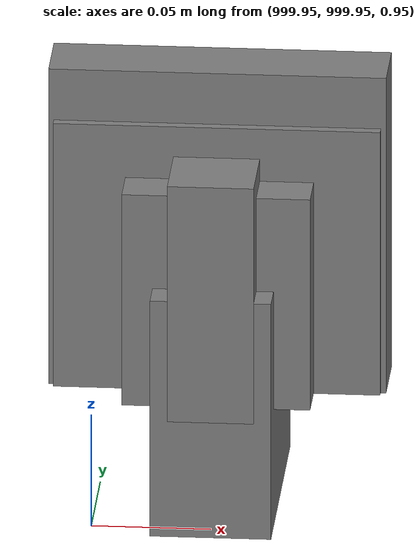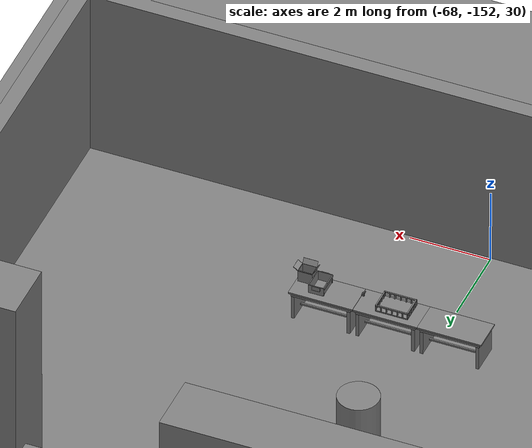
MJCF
<mujoco>
    <option gravity="0.000000000 0.000000000 -9.810000420" timestep="0.0049999999" integrator="implicitfast" density="1.225" viscosity="1.8000001e-05" noslip_iterations="10" iterations="100" sdf_iterations="50">
        <flag multiccd="disable"/>
    </option>
    <size memory="1000M"/>
    <compiler coordinate="local"/>
    <worldbody>
        <light cutoff="30" pos="0 1 1" dir="0 -1 -2"/>
        <light cutoff="30" pos="0 -1 1" dir="0 1 -2"/>
        <body pos="-64.866622925 -149.383972168 30.183746338" euler="89.999984741 89.999946594 0.000000000" name="openloong_gripper_2f85_fix_base_usda_bluebox_01">
            <geom contype="1" conaffinity="1" density="1000" type="box" material="" rgba="0.500000000 0.500000000 0.500000000 1.000000000" solimp="0.899999976 0.949999988 0.001000000" friction="1.000000000 0.005000000 0.000100000" solref="0.020000000 1.000000000" margin="0" condim="3" group="0" pos="0.276580811 0.187225342 0.000068665" quat="0.707106948 0.000077471 0.707106352 0.000077486" size="0.100000001 0.057999998 0.010000000" name="openloong_gripper_2f85_fix_base_usda_geom_4292716C_F4D3_4FC9_BAE6_7D48E8E1B4EC"/>
            <geom contype="1" conaffinity="1" density="1000" type="box" material="" rgba="0.500000000 0.500000000 0.500000000 1.000000000" solimp="0.899999976 0.949999988 0.001000000" friction="1.000000000 0.005000000 0.000100000" solref="0.020000000 1.000000000" margin="0" condim="3" group="0" pos="0.000000000 0.002883911 0.000000000" quat="0.999999881 0.000000000 0.000000000 0.000000000" size="0.254000008 0.003000000 0.172000006" name="openloong_gripper_2f85_fix_base_usda_geom_70DE90E2_9CEE_4A5C_88FD_7AAE6674C5BE"/>
            <geom contype="1" conaffinity="1" density="1000" type="box" material="" rgba="0.500000000 0.500000000 0.500000000 1.000000000" solimp="0.899999976 0.949999988 0.001000000" friction="1.000000000 0.005000000 0.000100000" solref="0.020000000 1.000000000" margin="0" condim="3" group="0" pos="0.000000000 0.124874115 0.173484802" quat="0.999796331 0.020176515 -0.000000015 0.000000030" size="0.259999990 0.119999997 0.007000000" name="openloong_gripper_2f85_fix_base_usda_geom_892D87DF_A4C3_4A55_B050_507A6C038E79"/>
            <geom contype="1" conaffinity="1" density="1000" type="box" material="" rgba="0.500000000 0.500000000 0.500000000 1.000000000" solimp="0.899999976 0.949999988 0.001000000" friction="1.000000000 0.005000000 0.000100000" solref="0.020000000 1.000000000" margin="0" condim="3" group="0" pos="0.000000000 0.124874115 -0.173469543" quat="0.999796331 -0.020176545 -0.000000015 0.000000000" size="0.259999990 0.119999997 0.007000000" name="openloong_gripper_2f85_fix_base_usda_geom_A34C37E3_CEB7_4307_9A67_11CA4568A4C0"/>
            <geom contype="1" conaffinity="1" density="1000" type="box" material="" rgba="0.500000000 0.500000000 0.500000000 1.000000000" solimp="0.899999976 0.949999988 0.001000000" friction="1.000000000 0.005000000 0.000100000" solref="0.020000000 1.000000000" margin="0" condim="3" group="0" pos="0.000000000 0.214008331 0.188980103" quat="0.999912977 0.013176724 0.000000015 0.000000000" size="0.259999990 0.029999999 0.012500000" name="openloong_gripper_2f85_fix_base_usda_geom_B7FF7660_FD8B_422F_A5F4_C0075CF6A447"/>
            <geom contype="1" conaffinity="1" density="1000" type="box" material="" rgba="0.500000000 0.500000000 0.500000000 1.000000000" solimp="0.899999976 0.949999988 0.001000000" friction="1.000000000 0.005000000 0.000100000" solref="0.020000000 1.000000000" margin="0" condim="3" group="0" pos="-0.258361816 0.125289917 0.001876831" quat="0.702796936 -0.020792112 0.710783124 0.020769298" size="0.189999998 0.119999997 0.009000000" name="openloong_gripper_2f85_fix_base_usda_geom_E8894224_B565_46BC_A146_FB8C089B050A"/>
            <geom contype="1" conaffinity="1" density="1000" type="box" material="" rgba="0.500000000 0.500000000 0.500000000 1.000000000" solimp="0.899999976 0.949999988 0.001000000" friction="1.000000000 0.005000000 0.000100000" solref="0.020000000 1.000000000" margin="0" condim="3" group="0" pos="0.000000000 0.214008331 -0.188980103" quat="0.999912977 -0.013176769 0.000000030 0.000000015" size="0.259999990 0.029999999 0.012500000" name="openloong_gripper_2f85_fix_base_usda_geom_463F34B6_EC4A_4652_9951_4530A022FF7C"/>
            <geom contype="1" conaffinity="1" density="1000" type="box" material="" rgba="0.500000000 0.500000000 0.500000000 1.000000000" solimp="0.899999976 0.949999988 0.001000000" friction="1.000000000 0.005000000 0.000100000" solref="0.020000000 1.000000000" margin="0" condim="3" group="0" pos="-0.276611328 0.187225342 0.000068665" quat="0.707106650 0.000077441 0.707106709 0.000077456" size="0.100000001 0.057999998 0.010000000" name="openloong_gripper_2f85_fix_base_usda_geom_0A357F28_6002_47F0_9435_1FC7706AB810"/>
            <geom contype="1" conaffinity="1" density="1000" type="box" material="" rgba="0.500000000 0.500000000 0.500000000 1.000000000" solimp="0.899999976 0.949999988 0.001000000" friction="1.000000000 0.005000000 0.000100000" solref="0.020000000 1.000000000" margin="0" condim="3" group="0" pos="0.258331299 0.125289917 0.001876831" quat="0.702851415 0.018856421 0.710823774 -0.019329369" size="0.189999998 0.119999997 0.009000000" name="openloong_gripper_2f85_fix_base_usda_geom_05F98004_35FD_4478_9377_B7F8C900B768"/>
            <freejoint name="openloong_gripper_2f85_fix_base_usda_bluebox_01_joint"/>
            <site size="0.005000000 0.005000000 0.005000000" rgba="0.500000000 0.500000000 0.500000000 1.000000000" pos="0.000000000 0.000000000 0.000000000" quat="0.999961913 0.008726534 0.000000000 0.000000000" group="0" type="sphere" name="openloong_gripper_2f85_fix_base_usda_bluebox_01site"/>
        </body>
        <body pos="-64.496299744 -149.491867065 30.235729218" euler="0.000000000 0.000000000 89.999946594" name="openloong_gripper_2f85_fix_base_usda_cardboardbox_01">
            <geom contype="1" conaffinity="1" density="1000" type="box" material="" rgba="0.500000000 0.500000000 0.500000000 1.000000000" solimp="0.899999976 0.949999988 0.001000000" friction="1.000000000 0.005000000 0.000100000" solref="0.020000000 1.000000000" margin="0" condim="3" group="0" pos="-0.003166199 -0.004086494 0.005052090" quat="1.000000000 0.000000000 0.000000000 0.000000000" size="0.142499998 0.177500010 0.005000000" name="openloong_gripper_2f85_fix_base_usda_geom_359C5669_DC16_4169_BC0B_1C7CE8702849"/>
            <geom contype="1" conaffinity="1" density="1000" type="box" material="" rgba="0.500000000 0.500000000 0.500000000 1.000000000" solimp="0.899999976 0.949999988 0.001000000" friction="1.000000000 0.005000000 0.000100000" solref="0.020000000 1.000000000" margin="0" condim="3" group="0" pos="-0.003166199 0.170316696 0.150570869" quat="1.000000000 0.000000000 0.000000000 0.000000000" size="0.142499998 0.005000000 0.149999991" name="openloong_gripper_2f85_fix_base_usda_geom_E3188936_9DBF_444F_81BE_035226A24132"/>
            <geom contype="1" conaffinity="1" density="1000" type="box" material="" rgba="0.500000000 0.500000000 0.500000000 1.000000000" solimp="0.899999976 0.949999988 0.001000000" friction="1.000000000 0.005000000 0.000100000" solref="0.020000000 1.000000000" margin="0" condim="3" group="0" pos="-0.147399902 -0.005307198 0.150570869" quat="1.000000000 0.000000000 0.000000000 0.000000000" size="0.005000000 0.177500010 0.149999991" name="openloong_gripper_2f85_fix_base_usda_geom_4578C1B4_9368_4702_88D5_23E1B06FE63B"/>
            <geom contype="1" conaffinity="1" density="1000" type="box" material="" rgba="0.500000000 0.500000000 0.500000000 1.000000000" solimp="0.899999976 0.949999988 0.001000000" friction="1.000000000 0.005000000 0.000100000" solref="0.020000000 1.000000000" margin="0" condim="3" group="0" pos="0.140275955 -0.005307198 0.150570869" quat="1.000000000 0.000000000 0.000000000 0.000000000" size="0.005000000 0.177500010 0.149999991" name="openloong_gripper_2f85_fix_base_usda_geom_B18B61DD_FCF9_4A60_A178_360387D351ED"/>
            <geom contype="1" conaffinity="1" density="1000" type="box" material="" rgba="0.500000000 0.500000000 0.500000000 1.000000000" solimp="0.899999976 0.949999988 0.001000000" friction="1.000000000 0.005000000 0.000100000" solref="0.020000000 1.000000000" margin="0" condim="3" group="0" pos="-0.003166199 -0.181550980 0.150570869" quat="1.000000000 0.000000000 0.000000000 0.000000000" size="0.142499998 0.005000000 0.149999991" name="openloong_gripper_2f85_fix_base_usda_geom_4103BA46_9944_4368_ACEB_4C411A3CCDC2"/>
            <freejoint name="openloong_gripper_2f85_fix_base_usda_cardboardbox_01_joint"/>
            <site size="0.005000000 0.005000000 0.005000000" rgba="0.500000000 0.500000000 0.500000000 1.000000000" pos="0.000000000 0.000000000 0.000000000" quat="0.999961913 0.008726535 0.000000000 0.000000000" group="0" type="sphere" name="openloong_gripper_2f85_fix_base_usda_site_F1D1DFF7_DB13_45B8_B8DD_EF8B654A0EE4"/>
            <body pos="0.139160156 -0.004048347 0.301930904" euler="-179.999954224 49.383502960 179.999954224" name="openloong_gripper_2f85_fix_base_usda_A1_006">
                <geom contype="1" conaffinity="1" density="1000" type="box" material="" rgba="0.500000000 0.500000000 0.500000000 1.000000000" solimp="0.899999976 0.949999988 0.001000000" friction="1.000000000 0.005000000 0.000100000" solref="0.020000000 1.000000000" margin="0" condim="3" group="0" pos="-0.071587563 0.000009537 0.001745224" quat="0.999999881 0.000000000 0.000000000 0.000000000" size="0.071249999 0.179999992 0.002500000" name="openloong_gripper_2f85_fix_base_usda_geom_EDE14143_E1E2_4C4F_B156_CF0968B31DB6"/>
                <joint armature="0" stiffness="0.07" damping="0.0099999998" axis="0.000000 1.000000 0.000000" type="hinge" name="openloong_gripper_2f85_fix_base_usda_A1_006"/>
            </body>
            <body pos="-0.145902634 -0.004086494 0.301938057" euler="-180.000000000 -60.000011444 -180.000000000" name="openloong_gripper_2f85_fix_base_usda_A2_006">
                <geom contype="1" conaffinity="1" density="1000" type="box" material="" rgba="0.500000000 0.500000000 0.500000000 1.000000000" solimp="0.899999976 0.949999988 0.001000000" friction="1.000000000 0.005000000 0.000100000" solref="0.020000000 1.000000000" margin="0" condim="3" group="0" pos="0.071268082 0.000009537 0.002717972" quat="0.000002921 0.000000000 -0.000000030 0.999999881" size="0.071249999 0.179999992 0.002500000" name="openloong_gripper_2f85_fix_base_usda_geom_E371D385_6D89_4124_A877_2D7277470435"/>
                <joint armature="0" stiffness="0.07" damping="0.0099999998" axis="0.000000 1.000000 0.000000" type="hinge" name="openloong_gripper_2f85_fix_base_usda_A2_006"/>
            </body>
            <body pos="-0.003385544 0.175991058 0.301930904" euler="-125.858116150 -0.000004561 0.000002331" name="openloong_gripper_2f85_fix_base_usda_B2_006">
                <geom contype="1" conaffinity="1" density="1000" type="box" material="" rgba="0.500000000 0.500000000 0.500000000 1.000000000" solimp="0.899999976 0.949999988 0.001000000" friction="1.000000000 0.005000000 0.000100000" solref="0.020000000 1.000000000" margin="0" condim="3" group="0" pos="0.000009537 -0.070939064 -0.002470016" quat="0.999614120 0.027776197 -0.000000015 0.000000030" size="0.137500003 0.064999998 0.005000000" name="openloong_gripper_2f85_fix_base_usda_geom_7B4BE8EF_6798_40BC_B017_7F47357E86FA"/>
                <joint armature="0" stiffness="0.07" damping="0.0099999998" axis="1.000000 0.000000 0.000000" type="hinge" name="openloong_gripper_2f85_fix_base_usda_B2_006"/>
            </body>
            <body pos="-0.003385544 -0.184140205 0.301938057" euler="147.805557251 0.000000000 0.000000000" name="openloong_gripper_2f85_fix_base_usda_B1_006">
                <geom contype="1" conaffinity="1" density="1000" type="box" material="" rgba="0.500000000 0.500000000 0.500000000 1.000000000" solimp="0.899999976 0.949999988 0.001000000" friction="1.000000000 0.005000000 0.000100000" solref="0.020000000 1.000000000" margin="0" condim="3" group="0" pos="-0.000028610 0.070202351 -0.002703667" quat="0.999614179 -0.027776167 0.000000000 0.000000000" size="0.137500003 0.064999998 0.005000000" name="openloong_gripper_2f85_fix_base_usda_geom_628F7A10_F86A_4ADC_A091_48CE5B3FC0F6"/>
                <joint armature="0" stiffness="0.07" damping="0.0099999998" axis="1.000000 0.000000 0.000000" type="hinge" name="openloong_gripper_2f85_fix_base_usda_B1_006"/>
            </body>
        </body>
        <body pos="-65.882858276 -149.481979370 30.229999542" euler="-64.487716675 0.000000000 0.000000000" name="openloong_gripper_2f85_fix_base_usda_Barcode">
            <geom contype="1" conaffinity="1" density="1000" type="box" material="" rgba="0.500000000 0.500000000 0.500000000 1.000000000" solimp="0.899999976 0.949999988 0.001000000" friction="1.000000000 0.005000000 0.000100000" solref="0.020000000 1.000000000" margin="0" condim="3" group="0" pos="0.000000000 0.013038635 0.001419067" quat="0.000000000 0.000000000 0.000000000 1.000000119" size="0.034000002 0.010000000 0.017999999" name="openloong_gripper_2f85_fix_base_usda_geom_C8B058C5_CFAC_4C1B_84D2_F8A0D8AC53DF"/>
            <geom contype="1" conaffinity="1" density="1000" type="box" material="" rgba="0.500000000 0.500000000 0.500000000 1.000000000" solimp="0.899999976 0.949999988 0.001000000" friction="1.000000000 0.005000000 0.000100000" solref="0.020000000 1.000000000" margin="0" condim="3" group="0" pos="0.000000000 -0.035301208 -0.007095337" quat="0.000000000 0.000000000 -0.043619365 0.999048233" size="0.028999999 0.010000000 0.020000000" name="openloong_gripper_2f85_fix_base_usda_geom_19545D08_1953_4E70_BA30_84C3A95B86AC"/>
            <geom contype="1" conaffinity="1" density="1000" type="box" material="" rgba="0.500000000 0.500000000 0.500000000 1.000000000" solimp="0.899999976 0.949999988 0.001000000" friction="1.000000000 0.005000000 0.000100000" solref="0.020000000 1.000000000" margin="0" condim="3" group="0" pos="0.000000000 -0.043411255 -0.011749268" quat="0.922262907 0.386563420 0.000000000 0.000000000" size="0.026000001 0.010000000 0.020000000" name="openloong_gripper_2f85_fix_base_usda_geom_4089A024_7E67_468A_8117_98EF0A1F2C94"/>
            <geom contype="1" conaffinity="1" density="1000" type="box" material="" rgba="0.500000000 0.500000000 0.500000000 1.000000000" solimp="0.899999976 0.949999988 0.001000000" friction="1.000000000 0.005000000 0.000100000" solref="0.020000000 1.000000000" margin="0" condim="3" group="0" pos="0.000000000 -0.016967773 -0.031860352" quat="0.000000000 0.000000000 0.000000000 1.000000119" size="0.008000000 0.010000000 0.013000000" name="openloong_gripper_2f85_fix_base_usda_geom_79835F39_1472_466A_8FB5_65C6B44081E8"/>
            <geom contype="1" conaffinity="1" density="1000" type="box" material="" rgba="0.500000000 0.500000000 0.500000000 1.000000000" solimp="0.899999976 0.949999988 0.001000000" friction="1.000000000 0.005000000 0.000100000" solref="0.020000000 1.000000000" margin="0" condim="3" group="0" pos="0.000000000 -0.001869202 0.000312805" quat="0.953716993 0.300705761 0.000000000 0.000000000" size="0.032000002 0.010000000 0.018999999" name="openloong_gripper_2f85_fix_base_usda_geom_D05D0D24_B2A7_44B6_93C7_D5CD1B82F601"/>
            <geom contype="1" conaffinity="1" density="1000" type="box" material="" rgba="0.500000000 0.500000000 0.500000000 1.000000000" solimp="0.899999976 0.949999988 0.001000000" friction="1.000000000 0.005000000 0.000100000" solref="0.020000000 1.000000000" margin="0" condim="3" group="0" pos="0.000000000 -0.019531250 -0.003173828" quat="0.953716993 0.300705761 0.000000000 0.000000000" size="0.030999999 0.010000000 0.020000000" name="openloong_gripper_2f85_fix_base_usda_geom_433E3AA4_CABE_41F0_B58C_CCB470D01105"/>
            <geom contype="1" conaffinity="1" density="1000" type="box" material="" rgba="0.500000000 0.500000000 0.500000000 1.000000000" solimp="0.899999976 0.949999988 0.001000000" friction="1.000000000 0.005000000 0.000100000" solref="0.020000000 1.000000000" margin="0" condim="3" group="0" pos="0.000000000 -0.035301208 -0.007095337" quat="0.953716993 0.300705761 0.000000000 0.000000000" size="0.028999999 0.010000000 0.020000000" name="openloong_gripper_2f85_fix_base_usda_geom_0C5B859B_F121_4510_B51A_844954339848"/>
            <geom contype="1" conaffinity="1" density="1000" type="box" material="" rgba="0.500000000 0.500000000 0.500000000 1.000000000" solimp="0.899999976 0.949999988 0.001000000" friction="1.000000000 0.005000000 0.000100000" solref="0.020000000 1.000000000" margin="0" condim="3" group="0" pos="0.000000000 -0.042617798 -0.071121216" quat="0.000000000 0.000000000 0.000000000 1.000000119" size="0.013000000 0.021000000 0.059999999" name="openloong_gripper_2f85_fix_base_usda_geom_7467C90B_6C02_41E5_BEFE_9996B28DAF38"/>
            <freejoint name="openloong_gripper_2f85_fix_base_usda_Barcode_joint"/>
            <site size="0.005000000 0.005000000 0.005000000" rgba="0.500000000 0.500000000 0.500000000 1.000000000" pos="0.000000000 0.000000000 0.000000000" quat="1.000000000 0.000000000 0.000000000 0.000000000" group="0" type="sphere" name="openloong_gripper_2f85_fix_base_usda_Barcode_site"/>
        </body>
        <body pos="-66.745018005 -149.392349243 30.184000015" euler="0.000000000 0.000000000 89.999946594" name="[22333467180736]_Basket_01">
            <geom contype="1" conaffinity="1" density="1000" type="box" material="" rgba="0.500000000 0.500000000 0.500000000 1.000000000" solimp="0.899999976 0.949999988 0.001000000" friction="1.000000000 0.005000000 0.000100000" solref="0.020000000 1.000000000" margin="0" condim="3" group="0" pos="-0.052425385 0.389207840 0.089787483" quat="0.707107008 0.000000000 0.000000000 0.707106411" size="0.014249999 0.014249999 0.059999999" name="[22333467180736]_geom_1C4092B3_315C_4C9C_8D11_45C14CE6AD45"/>
            <geom contype="1" conaffinity="1" density="1000" type="box" material="" rgba="0.500000000 0.500000000 0.500000000 1.000000000" solimp="0.899999976 0.949999988 0.001000000" friction="1.000000000 0.005000000 0.000100000" solref="0.020000000 1.000000000" margin="0" condim="3" group="0" pos="0.264015198 -0.133043289 0.089787483" quat="0.707107008 0.000000000 0.000000000 0.707106411" size="0.014249999 0.014249999 0.059999999" name="[22333467180736]_geom_3D4C5DCE_C8C0_45F1_980F_6FAE8560FCA5"/>
            <geom contype="1" conaffinity="1" density="1000" type="box" material="" rgba="0.500000000 0.500000000 0.500000000 1.000000000" solimp="0.899999976 0.949999988 0.001000000" friction="1.000000000 0.005000000 0.000100000" solref="0.020000000 1.000000000" margin="0" condim="3" group="0" pos="-0.264015198 -0.265548706 0.089793205" quat="0.707107008 0.000000000 0.000000000 0.707106411" size="0.014249999 0.014249999 0.059999999" name="[22333467180736]_geom_EB85FFE2_A5E0_4FF3_9858_8674464B4270"/>
            <geom contype="1" conaffinity="1" density="1000" type="box" material="" rgba="0.500000000 0.500000000 0.500000000 1.000000000" solimp="0.899999976 0.949999988 0.001000000" friction="1.000000000 0.005000000 0.000100000" solref="0.020000000 1.000000000" margin="0" condim="3" group="0" pos="-0.160263062 -0.389322281 0.089793205" quat="0.707107008 0.000000000 0.000000000 0.707106411" size="0.014249999 0.014249999 0.059999999" name="[22333467180736]_geom_EDBB2460_4A4A_413E_9E22_AD1A7A5223FE"/>
            <geom contype="1" conaffinity="1" density="1000" type="box" material="" rgba="0.500000000 0.500000000 0.500000000 1.000000000" solimp="0.899999976 0.949999988 0.001000000" friction="1.000000000 0.005000000 0.000100000" solref="0.020000000 1.000000000" margin="0" condim="3" group="0" pos="0.162265778 -0.389322281 0.089787483" quat="0.707107008 0.000000000 0.000000000 0.707106411" size="0.014249999 0.014249999 0.059999999" name="[22333467180736]_geom_0CD7386E_80E0_460D_86E8_B1C27BD3E150"/>
            <geom contype="1" conaffinity="1" density="1000" type="box" material="" rgba="0.500000000 0.500000000 0.500000000 1.000000000" solimp="0.899999976 0.949999988 0.001000000" friction="1.000000000 0.005000000 0.000100000" solref="0.020000000 1.000000000" margin="0" condim="3" group="0" pos="0.264015198 0.389207840 0.089787483" quat="0.707107008 0.000000000 0.000000000 0.707106411" size="0.014249999 0.014249999 0.059999999" name="[22333467180736]_geom_FB11A741_7A13_4D69_A04A_BB4926EF6FC7"/>
            <geom contype="1" conaffinity="1" density="1000" type="box" material="" rgba="0.500000000 0.500000000 0.500000000 1.000000000" solimp="0.899999976 0.949999988 0.001000000" friction="1.000000000 0.005000000 0.000100000" solref="0.020000000 1.000000000" margin="0" condim="3" group="0" pos="-0.264015198 -0.133043289 0.089793205" quat="0.707107008 0.000000000 0.000000000 0.707106411" size="0.014249999 0.014249999 0.059999999" name="[22333467180736]_geom_3C9A1F7C_21E7_4EA0_9B92_98AB6FC8A7B9"/>
            <geom contype="1" conaffinity="1" density="1000" type="box" material="" rgba="0.500000000 0.500000000 0.500000000 1.000000000" solimp="0.899999976 0.949999988 0.001000000" friction="1.000000000 0.005000000 0.000100000" solref="0.020000000 1.000000000" margin="0" condim="3" group="0" pos="-0.264026642 0.269256592 0.089793205" quat="0.707107008 0.000000000 0.000000000 0.707106411" size="0.014249999 0.014249999 0.059999999" name="[22333467180736]_geom_AA274D16_2EEF_43DC_847E_A9E6F4E74780"/>
            <geom contype="1" conaffinity="1" density="1000" type="box" material="" rgba="0.500000000 0.500000000 0.500000000 1.000000000" solimp="0.899999976 0.949999988 0.001000000" friction="1.000000000 0.005000000 0.000100000" solref="0.020000000 1.000000000" margin="0" condim="3" group="0" pos="0.054462433 0.389207840 0.089787483" quat="0.707107008 0.000000000 0.000000000 0.707106411" size="0.014249999 0.014249999 0.059999999" name="[22333467180736]_geom_7EF7040B_FB25_4F2F_8462_0F15A9137E78"/>
            <geom contype="1" conaffinity="1" density="1000" type="box" material="" rgba="0.500000000 0.500000000 0.500000000 1.000000000" solimp="0.899999976 0.949999988 0.001000000" friction="1.000000000 0.005000000 0.000100000" solref="0.020000000 1.000000000" margin="0" condim="3" group="0" pos="0.054462433 -0.389322281 0.089787483" quat="0.707107008 0.000000000 0.000000000 0.707106411" size="0.014249999 0.014249999 0.059999999" name="[22333467180736]_geom_A1218E7E_185B_4981_BB97_8A30F62A9459"/>
            <geom contype="1" conaffinity="1" density="1000" type="box" material="" rgba="0.500000000 0.500000000 0.500000000 1.000000000" solimp="0.899999976 0.949999988 0.001000000" friction="1.000000000 0.005000000 0.000100000" solref="0.020000000 1.000000000" margin="0" condim="3" group="0" pos="0.264015198 0.269256592 0.089793205" quat="0.707107008 0.000000000 0.000000000 0.707106411" size="0.014249999 0.014249999 0.059999999" name="[22333467180736]_geom_57FF7EAD_DD12_40EE_B77D_69D7636643EC"/>
            <geom contype="1" conaffinity="1" density="1000" type="box" material="" rgba="0.500000000 0.500000000 0.500000000 1.000000000" solimp="0.899999976 0.949999988 0.001000000" friction="1.000000000 0.005000000 0.000100000" solref="0.020000000 1.000000000" margin="0" condim="3" group="0" pos="0.264015198 -0.389322281 0.089787483" quat="0.707107008 0.000000000 0.000000000 0.707106411" size="0.014249999 0.014249999 0.059999999" name="[22333467180736]_geom_F51F01B7_9073_4BF7_903A_C68E22EDCEB0"/>
            <geom contype="1" conaffinity="1" density="1000" type="box" material="" rgba="0.500000000 0.500000000 0.500000000 1.000000000" solimp="0.899999976 0.949999988 0.001000000" friction="1.000000000 0.005000000 0.000100000" solref="0.020000000 1.000000000" margin="0" condim="3" group="0" pos="0.000000000 0.000000000 0.015998840" quat="0.707107008 0.000000000 0.000000000 0.707106411" size="0.403499991 0.279000014 0.015750000" name="[22333467180736]_geom_C1115DE6_0CBF_4D25_B769_16AC3655EDF2"/>
            <geom contype="1" conaffinity="1" density="1000" type="box" material="" rgba="0.500000000 0.500000000 0.500000000 1.000000000" solimp="0.899999976 0.949999988 0.001000000" friction="1.000000000 0.005000000 0.000100000" solref="0.020000000 1.000000000" margin="0" condim="3" group="0" pos="0.000000000 -0.389476776 0.163619041" quat="0.707107008 0.000000000 0.000000000 0.707106411" size="0.015000000 0.277500004 0.015750000" name="[22333467180736]_geom_5A251E90_77C5_42EF_87A5_0E38A44167E8"/>
            <geom contype="1" conaffinity="1" density="1000" type="box" material="" rgba="0.500000000 0.500000000 0.500000000 1.000000000" solimp="0.899999976 0.949999988 0.001000000" friction="1.000000000 0.005000000 0.000100000" solref="0.020000000 1.000000000" margin="0" condim="3" group="0" pos="0.162265778 0.389207840 0.089787483" quat="0.707107008 0.000000000 0.000000000 0.707106411" size="0.014249999 0.014249999 0.059999999" name="[22333467180736]_geom_BE569AEE_8F4B_4A5E_98CF_4C619D1B8F7A"/>
            <geom contype="1" conaffinity="1" density="1000" type="box" material="" rgba="0.500000000 0.500000000 0.500000000 1.000000000" solimp="0.899999976 0.949999988 0.001000000" friction="1.000000000 0.005000000 0.000100000" solref="0.020000000 1.000000000" margin="0" condim="3" group="0" pos="0.000000000 0.389471054 0.163619041" quat="0.707107008 0.000000000 0.000000000 0.707106411" size="0.015000000 0.277500004 0.015750000" name="[22333467180736]_geom_65B33156_E026_4C7B_8C9A_A804DF91B750"/>
            <geom contype="1" conaffinity="1" density="1000" type="box" material="" rgba="0.500000000 0.500000000 0.500000000 1.000000000" solimp="0.899999976 0.949999988 0.001000000" friction="1.000000000 0.005000000 0.000100000" solref="0.020000000 1.000000000" margin="0" condim="3" group="0" pos="-0.263511658 0.000000000 0.163619041" quat="0.707107008 0.000000000 0.000000000 0.707106411" size="0.403499991 0.015000000 0.015750000" name="[22333467180736]_geom_E499338E_C40D_45C8_AB51_592C304C24CC"/>
            <geom contype="1" conaffinity="1" density="1000" type="box" material="" rgba="0.500000000 0.500000000 0.500000000 1.000000000" solimp="0.899999976 0.949999988 0.001000000" friction="1.000000000 0.005000000 0.000100000" solref="0.020000000 1.000000000" margin="0" condim="3" group="0" pos="-0.264015198 0.141334534 0.089793205" quat="0.707107008 0.000000000 0.000000000 0.707106411" size="0.014249999 0.014249999 0.059999999" name="[22333467180736]_geom_277FE7A3_E03C_4693_91BD_8A73AAEBF6E0"/>
            <geom contype="1" conaffinity="1" density="1000" type="box" material="" rgba="0.500000000 0.500000000 0.500000000 1.000000000" solimp="0.899999976 0.949999988 0.001000000" friction="1.000000000 0.005000000 0.000100000" solref="0.020000000 1.000000000" margin="0" condim="3" group="0" pos="0.264015198 -0.265548706 0.089787483" quat="0.707107008 0.000000000 0.000000000 0.707106411" size="0.014249999 0.014249999 0.059999999" name="[22333467180736]_geom_F7B3F89D_31F0_4158_9CB6_4B94E5545E44"/>
            <geom contype="1" conaffinity="1" density="1000" type="box" material="" rgba="0.500000000 0.500000000 0.500000000 1.000000000" solimp="0.899999976 0.949999988 0.001000000" friction="1.000000000 0.005000000 0.000100000" solref="0.020000000 1.000000000" margin="0" condim="3" group="0" pos="-0.160263062 0.389207840 0.089787483" quat="0.707107008 0.000000000 0.000000000 0.707106411" size="0.014249999 0.014249999 0.059999999" name="[22333467180736]_geom_83006B3A_4E48_44F2_93F4_F1B65268FF44"/>
            <geom contype="1" conaffinity="1" density="1000" type="box" material="" rgba="0.500000000 0.500000000 0.500000000 1.000000000" solimp="0.899999976 0.949999988 0.001000000" friction="1.000000000 0.005000000 0.000100000" solref="0.020000000 1.000000000" margin="0" condim="3" group="0" pos="-0.052425385 -0.389322281 0.089787483" quat="0.707107008 0.000000000 0.000000000 0.707106411" size="0.014249999 0.014249999 0.059999999" name="[22333467180736]_geom_3F65CCAF_7E35_4574_B0D1_68FD52F33FE9"/>
            <geom contype="1" conaffinity="1" density="1000" type="box" material="" rgba="0.500000000 0.500000000 0.500000000 1.000000000" solimp="0.899999976 0.949999988 0.001000000" friction="1.000000000 0.005000000 0.000100000" solref="0.020000000 1.000000000" margin="0" condim="3" group="0" pos="-0.264026642 -0.389322281 0.089793205" quat="0.707107008 0.000000000 0.000000000 0.707106411" size="0.014249999 0.014249999 0.059999999" name="[22333467180736]_geom_D71378BE_41D8_47A3_B63C_A770CD38271A"/>
            <geom contype="1" conaffinity="1" density="1000" type="box" material="" rgba="0.500000000 0.500000000 0.500000000 1.000000000" solimp="0.899999976 0.949999988 0.001000000" friction="1.000000000 0.005000000 0.000100000" solref="0.020000000 1.000000000" margin="0" condim="3" group="0" pos="0.264015198 0.141334534 0.089787483" quat="0.707107008 0.000000000 0.000000000 0.707106411" size="0.014249999 0.014249999 0.059999999" name="[22333467180736]_geom_D32D8C35_BA1A_4F68_908C_B8563EAAFBB2"/>
            <geom contype="1" conaffinity="1" density="1000" type="box" material="" rgba="0.500000000 0.500000000 0.500000000 1.000000000" solimp="0.899999976 0.949999988 0.001000000" friction="1.000000000 0.005000000 0.000100000" solref="0.020000000 1.000000000" margin="0" condim="3" group="0" pos="-0.264015198 0.389207840 0.089793205" quat="0.707107008 0.000000000 0.000000000 0.707106411" size="0.014249999 0.014249999 0.059999999" name="[22333467180736]_geom_9E19F425_8CF1_46D3_9F06_0FD2FC7A0B6C"/>
            <geom contype="1" conaffinity="1" density="1000" type="box" material="" rgba="0.500000000 0.500000000 0.500000000 1.000000000" solimp="0.899999976 0.949999988 0.001000000" friction="1.000000000 0.005000000 0.000100000" solref="0.020000000 1.000000000" margin="0" condim="3" group="0" pos="0.264015198 0.004480362 0.089787483" quat="0.707107008 0.000000000 0.000000000 0.707106411" size="0.014249999 0.014249999 0.059999999" name="[22333467180736]_geom_5CD8AF92_764A_48D5_884C_A4D4160602D5"/>
            <geom contype="1" conaffinity="1" density="1000" type="box" material="" rgba="0.500000000 0.500000000 0.500000000 1.000000000" solimp="0.899999976 0.949999988 0.001000000" friction="1.000000000 0.005000000 0.000100000" solref="0.020000000 1.000000000" margin="0" condim="3" group="0" pos="0.263694763 -0.000011444 0.163619041" quat="0.707107008 0.000000000 0.000000000 0.707106411" size="0.403499991 0.015000000 0.015750000" name="[22333467180736]_geom_2112ABB3_059A_41B9_8034_D73D5B73DFD9"/>
            <geom contype="1" conaffinity="1" density="1000" type="box" material="" rgba="0.500000000 0.500000000 0.500000000 1.000000000" solimp="0.899999976 0.949999988 0.001000000" friction="1.000000000 0.005000000 0.000100000" solref="0.020000000 1.000000000" margin="0" condim="3" group="0" pos="-0.264015198 0.004480362 0.089793205" quat="0.707107008 0.000000000 0.000000000 0.707106411" size="0.014249999 0.014249999 0.059999999" name="[22333467180736]_geom_4E3322CC_936C_4D65_B03A_BDEE8EA56957"/>
            <freejoint name="[22333467180736]_joint_22A22F22_7F46_45D7_B8CA_AC216EE1B78F"/>
        </body>
        <body pos="0.000000000 0.000000000 0.000000000" euler="0.000000000 0.000000000 0.000000000" name="Static Objects_Static Objects">
            <geom contype="1" conaffinity="1" density="1000" type="box" material="" rgba="0.500000000 0.500000000 0.500000000 1.000000000" solimp="0.899999976 0.949999988 0.001000000" friction="1.000000000 0.005000000 0.000100000" solref="0.020000000 1.000000000" margin="0" condim="3" group="0" pos="-67.544113159 -149.365814209 29.727830887" quat="0.500000417 0.499999970 0.499999553 0.499999970" size="0.381000012 0.319999993 0.041000001" name="Static Objects_geom_9DE94348_A759_40CE_8C8E_FCC410C0019E"/>
            <geom contype="1" conaffinity="1" density="1000" type="box" material="" rgba="0.500000000 0.500000000 0.500000000 1.000000000" solimp="0.899999976 0.949999988 0.001000000" friction="1.000000000 0.005000000 0.000100000" solref="0.020000000 1.000000000" margin="0" condim="3" group="0" pos="-68.239501953 -149.365814209 30.086868286" quat="0.500000417 0.499999970 0.499999553 0.499999970" size="0.370999992 0.039500002 0.745000005" name="Static Objects_geom_30F07E3D_9377_4EEA_ACA8_E34BC37B4C84"/>
            <geom contype="1" conaffinity="1" density="1000" type="box" material="" rgba="0.500000000 0.500000000 0.500000000 1.000000000" solimp="0.899999976 0.949999988 0.001000000" friction="1.000000000 0.005000000 0.000100000" solref="0.020000000 1.000000000" margin="0" condim="3" group="0" pos="-68.239501953 -149.365814209 30.147235870" quat="0.500000417 0.499999970 0.499999553 0.499999970" size="0.400000006 0.022000000 0.800000012" name="Static Objects_geom_5E8CBA68_3D5C_48EC_9FA8_DF3754FCDB74"/>
            <geom contype="1" conaffinity="1" density="1000" type="box" material="" rgba="0.500000000 0.500000000 0.500000000 1.000000000" solimp="0.899999976 0.949999988 0.001000000" friction="1.000000000 0.005000000 0.000100000" solref="0.020000000 1.000000000" margin="0" condim="3" group="0" pos="-68.934890747 -149.365814209 29.727830887" quat="0.500000417 0.499999970 0.499999553 0.499999970" size="0.381000012 0.319999993 0.041000001" name="Static Objects_geom_2B36AEAA_0098_4468_806C_65B1D7802CEA"/>
            <geom contype="1" conaffinity="1" density="1000" type="box" material="" rgba="0.500000000 0.500000000 0.500000000 1.000000000" solimp="0.899999976 0.949999988 0.001000000" friction="1.000000000 0.005000000 0.000100000" solref="0.020000000 1.000000000" margin="0" condim="3" group="0" pos="-68.239501953 -149.365814209 29.561563492" quat="0.500000417 0.499999970 0.499999553 0.499999970" size="0.020000000 0.022000000 0.660000026" name="Static Objects_geom_F83161AF_4EA1_4B39_A700_8F7CFDC0D2D8"/>
            <geom contype="1" conaffinity="1" density="1000" type="box" material="" rgba="0.500000000 0.500000000 0.500000000 1.000000000" solimp="0.899999976 0.949999988 0.001000000" friction="1.000000000 0.005000000 0.000100000" solref="0.020000000 1.000000000" margin="0" condim="3" group="0" pos="-65.945671082 -149.365814209 29.727830887" quat="0.500000417 0.499999970 0.499999553 0.499999970" size="0.381000012 0.319999993 0.041000001" name="Static Objects_geom_928D7A62_F1F8_489C_98FA_8387DEB2A9A3"/>
            <geom contype="1" conaffinity="1" density="1000" type="box" material="" rgba="0.500000000 0.500000000 0.500000000 1.000000000" solimp="0.899999976 0.949999988 0.001000000" friction="1.000000000 0.005000000 0.000100000" solref="0.020000000 1.000000000" margin="0" condim="3" group="0" pos="-66.641059875 -149.365814209 30.086868286" quat="0.500000417 0.499999970 0.499999553 0.499999970" size="0.370999992 0.039500002 0.745000005" name="Static Objects_geom_D209D85D_16FD_474E_8F11_F7346B0B50DB"/>
            <geom contype="1" conaffinity="1" density="1000" type="box" material="" rgba="0.500000000 0.500000000 0.500000000 1.000000000" solimp="0.899999976 0.949999988 0.001000000" friction="1.000000000 0.005000000 0.000100000" solref="0.020000000 1.000000000" margin="0" condim="3" group="0" pos="-66.641059875 -149.365814209 30.147235870" quat="0.500000417 0.499999970 0.499999553 0.499999970" size="0.400000006 0.022000000 0.800000012" name="Static Objects_geom_50D01888_F84D_44DE_8EE7_1CAD5174BA7C"/>
            <geom contype="1" conaffinity="1" density="1000" type="box" material="" rgba="0.500000000 0.500000000 0.500000000 1.000000000" solimp="0.899999976 0.949999988 0.001000000" friction="1.000000000 0.005000000 0.000100000" solref="0.020000000 1.000000000" margin="0" condim="3" group="0" pos="-67.336448669 -149.365814209 29.727830887" quat="0.500000417 0.499999970 0.499999553 0.499999970" size="0.381000012 0.319999993 0.041000001" name="Static Objects_geom_7AD8A85B_9894_40E0_8A34_36CB09689ED8"/>
            <geom contype="1" conaffinity="1" density="1000" type="box" material="" rgba="0.500000000 0.500000000 0.500000000 1.000000000" solimp="0.899999976 0.949999988 0.001000000" friction="1.000000000 0.005000000 0.000100000" solref="0.020000000 1.000000000" margin="0" condim="3" group="0" pos="-66.641059875 -149.365814209 29.561563492" quat="0.500000417 0.499999970 0.499999553 0.499999970" size="0.020000000 0.022000000 0.660000026" name="Static Objects_geom_56F4A141_4E64_4CEF_908A_7564C0A3B17B"/>
            <geom contype="1" conaffinity="1" density="1000" type="box" material="" rgba="0.500000000 0.500000000 0.500000000 1.000000000" solimp="0.899999976 0.949999988 0.001000000" friction="1.000000000 0.005000000 0.000100000" solref="0.020000000 1.000000000" margin="0" condim="3" group="0" pos="-64.338577271 -149.365814209 29.727830887" quat="0.500000417 0.499999970 0.499999553 0.499999970" size="0.381000012 0.319999993 0.041000001" name="Static Objects_geom_135D5AB9_52BA_4E61_8E8F_41D6C4358781"/>
            <geom contype="1" conaffinity="1" density="1000" type="box" material="" rgba="0.500000000 0.500000000 0.500000000 1.000000000" solimp="0.899999976 0.949999988 0.001000000" friction="1.000000000 0.005000000 0.000100000" solref="0.020000000 1.000000000" margin="0" condim="3" group="0" pos="-65.033966064 -149.365814209 30.086868286" quat="0.500000417 0.499999970 0.499999553 0.499999970" size="0.370999992 0.039500002 0.745000005" name="Static Objects_geom_162CEC71_1A1A_4EA8_8856_2B0FEFA3E914"/>
            <geom contype="1" conaffinity="1" density="1000" type="box" material="" rgba="0.500000000 0.500000000 0.500000000 1.000000000" solimp="0.899999976 0.949999988 0.001000000" friction="1.000000000 0.005000000 0.000100000" solref="0.020000000 1.000000000" margin="0" condim="3" group="0" pos="-65.033966064 -149.365814209 30.147235870" quat="0.500000417 0.499999970 0.499999553 0.499999970" size="0.400000006 0.022000000 0.800000012" name="Static Objects_geom_72DB8522_AC75_4394_8C80_27E43977DF38"/>
            <geom contype="1" conaffinity="1" density="1000" type="box" material="" rgba="0.500000000 0.500000000 0.500000000 1.000000000" solimp="0.899999976 0.949999988 0.001000000" friction="1.000000000 0.005000000 0.000100000" solref="0.020000000 1.000000000" margin="0" condim="3" group="0" pos="-65.729354858 -149.365814209 29.727830887" quat="0.500000417 0.499999970 0.499999553 0.499999970" size="0.381000012 0.319999993 0.041000001" name="Static Objects_geom_19AEB03D_A9AE_4C2B_9F22_5839F2145F55"/>
            <geom contype="1" conaffinity="1" density="1000" type="box" material="" rgba="0.500000000 0.500000000 0.500000000 1.000000000" solimp="0.899999976 0.949999988 0.001000000" friction="1.000000000 0.005000000 0.000100000" solref="0.020000000 1.000000000" margin="0" condim="3" group="0" pos="-65.033966064 -149.365814209 29.561563492" quat="0.500000417 0.499999970 0.499999553 0.499999970" size="0.020000000 0.022000000 0.660000026" name="Static Objects_geom_4C3706C7_F93C_4BE4_82D9_C44CE7E738F0"/>
            <geom contype="1" conaffinity="1" density="1000" type="box" material="" rgba="0.500000000 0.500000000 0.500000000 1.000000000" solimp="0.899999976 0.949999988 0.001000000" friction="1.000000000 0.005000000 0.000100000" solref="0.020000000 1.000000000" margin="0" condim="3" group="0" pos="-61.754566193 -137.853729248 33.906845093" quat="0.707107067 0.000000000 0.000000000 0.707106471" size="0.759999990 0.759999990 4.500000000" name="Static Objects_geom_B80E8D59_C68F_46B7_82B9_AD912335F38F"/>
            <geom contype="1" conaffinity="1" density="1000" type="box" material="" rgba="0.500000000 0.500000000 0.500000000 1.000000000" solimp="0.899999976 0.949999988 0.001000000" friction="1.000000000 0.005000000 0.000100000" solref="0.020000000 1.000000000" margin="0" condim="3" group="0" pos="-57.511135101 -144.927108765 31.707921982" quat="1.000000000 0.000000000 0.000000000 0.000000000" size="0.200000003 8.000000000 2.299999952" name="Static Objects_geom_F43931DD_852F_41C8_B719_E182CC91CD02"/>
            <geom contype="1" conaffinity="1" density="1000" type="box" material="" rgba="0.500000000 0.500000000 0.500000000 1.000000000" solimp="0.899999976 0.949999988 0.001000000" friction="1.000000000 0.005000000 0.000100000" solref="0.020000000 1.000000000" margin="0" condim="3" group="0" pos="-80.517646790 -157.574050903 31.688196182" quat="0.707107067 0.000000000 0.000000000 0.707106471" size="0.600000024 0.600000024 2.299999952" name="Static Objects_geom_25719F24_7095_48B8_8007_04790E2F48DD"/>
            <geom contype="1" conaffinity="1" density="1000" type="box" material="" rgba="0.500000000 0.500000000 0.500000000 1.000000000" solimp="0.899999976 0.949999988 0.001000000" friction="1.000000000 0.005000000 0.000100000" solref="0.020000000 1.000000000" margin="0" condim="3" group="0" pos="-80.711044312 -147.414932251 31.666158676" quat="1.000000000 0.000000000 0.000000000 0.000000000" size="0.200000003 10.000000000 2.299999952" name="Static Objects_geom_1BCEF85D_5C2C_487C_ABBD_ADB744A108C0"/>
            <geom contype="1" conaffinity="1" density="1000" type="box" material="" rgba="0.500000000 0.500000000 0.500000000 1.000000000" solimp="0.899999976 0.949999988 0.001000000" friction="1.000000000 0.005000000 0.000100000" solref="0.020000000 1.000000000" margin="0" condim="3" group="0" pos="-57.687217712 -137.434692383 31.688196182" quat="0.707107067 0.000000000 0.000000000 0.707106471" size="0.600000024 0.600000024 2.299999952" name="Static Objects_geom_8EF85D56_EB8B_4956_B1A4_F57F8195E040"/>
            <geom contype="1" conaffinity="1" density="1000" type="box" material="" rgba="0.500000000 0.500000000 0.500000000 1.000000000" solimp="0.899999976 0.949999988 0.001000000" friction="1.000000000 0.005000000 0.000100000" solref="0.020000000 1.000000000" margin="0" condim="3" group="0" pos="-69.537033081 -140.263229370 31.714921951" quat="0.707107067 0.000000000 0.000000000 0.707106471" size="0.759999990 4.500000000 2.299999952" name="Static Objects_geom_D433D0B8_5CAB_4A4F_81B2_E3AF29EE1070"/>
            <geom contype="1" conaffinity="1" density="1000" type="box" material="" rgba="0.500000000 0.500000000 0.500000000 1.000000000" solimp="0.899999976 0.949999988 0.001000000" friction="1.000000000 0.005000000 0.000100000" solref="0.020000000 1.000000000" margin="0" condim="3" group="0" pos="-80.073638916 -137.853713989 33.906845093" quat="0.707107067 0.000000000 0.000000000 0.707106471" size="0.759999990 0.759999990 4.500000000" name="Static Objects_geom_C9272398_D01F_49FA_88E7_8A20231497BB"/>
            <geom contype="1" conaffinity="1" density="1000" type="box" material="" rgba="0.500000000 0.500000000 0.500000000 1.000000000" solimp="0.899999976 0.949999988 0.001000000" friction="1.000000000 0.005000000 0.000100000" solref="0.020000000 1.000000000" margin="0" condim="3" group="0" pos="-73.406707764 -155.734664917 31.707921982" quat="1.000000000 0.000000000 0.000000000 0.000000000" size="0.200000003 3.000000000 2.299999952" name="Static Objects_geom_2B16741A_364E_4924_AAAE_35C3EF312517"/>
            <geom contype="1" conaffinity="1" density="1000" type="box" material="" rgba="0.500000000 0.500000000 0.500000000 1.000000000" solimp="0.899999976 0.949999988 0.001000000" friction="1.000000000 0.005000000 0.000100000" solref="0.020000000 1.000000000" margin="0" condim="3" group="0" pos="-68.497543335 -137.448257446 31.707921982" quat="0.707107067 0.000000000 0.000000000 0.707106471" size="0.200000003 14.000000000 2.299999952" name="Static Objects_geom_23126B74_C61C_4339_89BD_28B7D40813B7"/>
            <geom contype="1" conaffinity="1" density="1000" type="cylinder" material="" rgba="0.500000000 0.500000000 0.500000000 1.000000000" solimp="0.899999976 0.949999988 0.001000000" friction="1.000000000 0.005000000 0.000100000" solref="0.020000000 1.000000000" margin="0" condim="3" group="0" pos="-68.868522644 -142.134506226 31.711090088" quat="0.707107067 0.000000000 0.000000000 0.707106471" size="0.509999990 2.299999952 1.000000000" name="Static Objects_geom_73B62370_372D_4417_8DA9_589F429FE860"/>
            <geom contype="1" conaffinity="1" density="1000" type="plane" material="" rgba="0.500000000 0.500000000 0.500000000 1.000000000" solimp="0.899999976 0.949999988 0.001000000" friction="1.000000000 0.005000000 0.000100000" solref="0.020000000 1.000000000" margin="0" condim="3" group="0" pos="-72.873703003 -147.131927490 29.409669876" quat="1.000000000 0.000000000 0.000000000 0.000000000" size="18.000000000 14.000000000 1.000000000" name="Static Objects_geom_B671FB0D_8B49_4926_BEEE_E61E88FEF7EB"/>
            <geom contype="1" conaffinity="1" density="1000" type="box" material="" rgba="0.500000000 0.500000000 0.500000000 1.000000000" solimp="0.899999976 0.949999988 0.001000000" friction="1.000000000 0.005000000 0.000100000" solref="0.020000000 1.000000000" margin="0" condim="3" group="0" pos="-79.943580627 -157.782272339 31.707921982" quat="0.707107067 0.000000000 0.000000000 0.707106471" size="0.200000003 7.000000000 2.299999952" name="Static Objects_geom_1F618D8B_4403_4645_9911_B281DC9037CE"/>
            <geom contype="1" conaffinity="1" density="1000" type="box" material="" rgba="0.500000000 0.500000000 0.500000000 1.000000000" solimp="0.899999976 0.949999988 0.001000000" friction="1.000000000 0.005000000 0.000100000" solref="0.020000000 1.000000000" margin="0" condim="3" group="0" pos="-65.421028137 -152.903442383 31.707921982" quat="0.707107067 0.000000000 0.000000000 0.707106471" size="0.200000003 7.800000191 2.299999952" name="Static Objects_geom_3C8EEC51_3AEA_482A_AB76_8CF3BF1186F0"/>
            <geom contype="1" conaffinity="1" density="1000" type="box" material="" rgba="0.500000000 0.500000000 0.500000000 1.000000000" solimp="0.899999976 0.949999988 0.001000000" friction="1.000000000 0.005000000 0.000100000" solref="0.020000000 1.000000000" margin="0" condim="3" group="0" pos="-74.776908875 -149.964416504 31.688196182" quat="1.000000000 0.000000000 0.000000000 0.000000000" size="0.600000024 0.409999996 2.299999952" name="Static Objects_geom_5C3772D7_8D1D_409F_8516_366C5DEF5EC4"/>
            <geom contype="1" conaffinity="1" density="1000" type="cylinder" material="" rgba="0.500000000 0.500000000 0.500000000 1.000000000" solimp="0.899999976 0.949999988 0.001000000" friction="1.000000000 0.005000000 0.000100000" solref="0.020000000 1.000000000" margin="0" condim="3" group="0" pos="-60.161884308 -142.134506226 31.711090088" quat="0.707107067 0.000000000 0.000000000 0.707106471" size="0.509999990 2.299999952 1.000000000" name="Static Objects_geom_F449D7CD_10A9_4A6D_9846_5B2B7D100C20"/>
            <geom contype="1" conaffinity="1" density="1000" type="cylinder" material="" rgba="0.500000000 0.500000000 0.500000000 1.000000000" solimp="0.899999976 0.949999988 0.001000000" friction="1.000000000 0.005000000 0.000100000" solref="0.020000000 1.000000000" margin="0" condim="3" group="0" pos="-75.382453918 -149.963455200 31.711090088" quat="0.707107067 0.000000000 0.000000000 0.707106471" size="0.409999996 2.299999952 1.000000000" name="Static Objects_geom_AFAAC29F_8F1E_4A70_91B5_8936CB691E11"/>
            <geom contype="1" conaffinity="1" density="1000" type="cylinder" material="" rgba="0.500000000 0.500000000 0.500000000 1.000000000" solimp="0.899999976 0.949999988 0.001000000" friction="1.000000000 0.005000000 0.000100000" solref="0.020000000 1.000000000" margin="0" condim="3" group="0" pos="-74.154960632 -149.963455200 31.711090088" quat="0.707107067 0.000000000 0.000000000 0.707106471" size="0.409999996 2.299999952 1.000000000" name="Static Objects_geom_6191322F_755C_4072_8A79_F48CC5662E6C"/>
            <geom contype="1" conaffinity="1" density="1000" type="cylinder" material="" rgba="0.500000000 0.500000000 0.500000000 1.000000000" solimp="0.899999976 0.949999988 0.001000000" friction="1.000000000 0.005000000 0.000100000" solref="0.020000000 1.000000000" margin="0" condim="3" group="0" pos="-77.566612244 -142.134506226 31.711090088" quat="0.707107067 0.000000000 0.000000000 0.707106471" size="0.509999990 2.299999952 1.000000000" name="Static Objects_geom_B7B36024_5BE0_4389_AA8E_6D5611DC0B7A"/>
        </body>
        <body pos="1000.000000000 999.999938965 1.000000000" euler="0.000000000 0.000000000 180.000000000" name="openloong_gripper_2f85_fix_base_usda_intelcore_i5">
            <geom contype="1" conaffinity="1" density="1000" type="box" material="" rgba="0.500000000 0.500000000 0.500000000 1.000000000" solimp="0.899999976 0.949999988 0.001000000" friction="1.000000000 0.005000000 0.000100000" solref="0.020000000 1.000000000" margin="0" condim="3" group="0" pos="0.000000000 0.000000000 0.051722717" quat="0.707106709 0.000000000 0.000000000 -0.707106769" size="0.052800000 0.018080002 0.052800000" name="openloong_gripper_2f85_fix_base_usda_geom_6EAD99F1_ED82_4C7E_B05F_2AD4BB1065FB"/>
            <freejoint name="openloong_gripper_2f85_fix_base_usda_intelcore_i5_joint"/>
            <site size="0.005000000 0.005000000 0.005000000" rgba="0.500000000 0.500000000 0.500000000 1.000000000" pos="0.000000000 0.000000000 0.000000000" quat="0.999961913 0.008726534 0.000000000 0.000000000" group="0" type="sphere" name="openloong_gripper_2f85_fix_base_usda_intelcore_i5site"/>
        </body>
        <body pos="-66.226921082 -148.926712036 31.168680191" euler="-106.458229065 -36.519050598 -56.220870972" mocap="true" name="spotlight1_SpotLight"/>
        <body pos="1000.000000000 1000.000000000 1.000000000" euler="0.000011953 0.000005123 -179.999984741" name="openloong_gripper_2f85_fix_base_usda_intel_box">
            <geom contype="1" conaffinity="1" density="1000" type="box" material="" rgba="0.500000000 0.500000000 0.500000000 1.000000000" solimp="0.899999976 0.949999988 0.001000000" friction="1.000000000 0.005000000 0.000100000" solref="0.020000000 1.000000000" margin="0" condim="3" group="0" pos="0.000000000 -0.000067139 0.000082284" quat="0.707106709 0.000000225 0.000000253 0.707106650" size="0.052800003 0.025300000 0.052800003" name="openloong_gripper_2f85_fix_base_usda_geom_46BBEEBD_5342_496A_B490_A81E19ABC770"/>
            <freejoint name="openloong_gripper_2f85_fix_base_usda_intel_box_joint"/>
            <site size="0.005000000 0.005000000 0.005000000" rgba="0.500000000 0.500000000 0.500000000 1.000000000" pos="0.000000000 0.000000000 0.000000000" quat="0.999961913 0.008726500 0.000000000 0.000000000" group="0" type="sphere" name="openloong_gripper_2f85_fix_base_usda_intel_boxsite"/>
        </body>
        <body pos="-66.003303528 -149.433364868 31.163742065" euler="147.393188477 89.617042542 153.396560669" mocap="true" name="spotlight2_SpotLight"/>
        <body pos="1000.000000000 1000.000000000 1.000000000" euler="0.000000000 0.000000000 180.000000000" name="openloong_gripper_2f85_fix_base_usda_wifi_box">
            <geom contype="1" conaffinity="1" density="1000" type="box" material="" rgba="0.500000000 0.500000000 0.500000000 1.000000000" solimp="0.899999976 0.949999988 0.001000000" friction="1.000000000 0.005000000 0.000100000" solref="0.020000000 1.000000000" margin="0" condim="3" group="0" pos="0.000000000 0.000000000 0.058978677" quat="0.000000000 0.000000047 0.000000000 1.000000000" size="0.068499997 0.018999999 0.059000000" name="openloong_gripper_2f85_fix_base_usda_geom_1E0AD924_B036_4EFC_85D2_E28E80CAFC0D"/>
            <freejoint name="openloong_gripper_2f85_fix_base_usda_wifi_box_joint"/>
            <site size="0.005000000 0.005000000 0.005000000" rgba="0.500000000 0.500000000 0.500000000 1.000000000" pos="0.000000000 0.000000000 0.000000000" quat="0.999961913 0.008726500 0.000000000 0.000000000" group="0" type="sphere" name="openloong_gripper_2f85_fix_base_usda_wifi_boxsite"/>
        </body>
        <body pos="1000.000000000 1000.000000000 1.000000000" euler="0.000000000 0.000000000 180.000000000" name="openloong_gripper_2f85_fix_base_usda_cpu_fan">
            <geom contype="1" conaffinity="1" density="1000" type="box" material="" rgba="0.500000000 0.500000000 0.500000000 1.000000000" solimp="0.899999976 0.949999988 0.001000000" friction="1.000000000 0.005000000 0.000100000" solref="0.020000000 1.000000000" margin="0" condim="3" group="0" pos="0.000000000 0.000000000 0.070034981" quat="0.000000000 0.000000000 0.000000000 1.000000000" size="0.070700005 0.014699999 0.070700005" name="openloong_gripper_2f85_fix_base_usda_geom_1A6AA53A_EC63_41BF_A667_DF450578275D"/>
            <freejoint name="openloong_gripper_2f85_fix_base_usda_cpu_fan_joint"/>
            <site size="0.005000000 0.005000000 0.005000000" rgba="0.500000000 0.500000000 0.500000000 1.000000000" pos="0.000000000 0.000000000 0.000000000" quat="0.999961913 0.008726535 0.000000000 0.000000000" group="0" type="sphere" name="openloong_gripper_2f85_fix_base_usda_cpu_fancsite"/>
        </body>
        <body pos="1000.000000000 1000.000000000 1.000000000" euler="0.000000000 0.000000000 180.000000000" name="openloong_gripper_2f85_fix_base_usda_battery_01">
            <geom contype="1" conaffinity="1" density="1000" type="box" material="" rgba="0.500000000 0.500000000 0.500000000 1.000000000" solimp="0.899999976 0.949999988 0.001000000" friction="1.000000000 0.005000000 0.000100000" solref="0.020000000 1.000000000" margin="0" condim="3" group="0" pos="-0.011123657 -0.041940309 0.101691343" quat="1.000000000 0.000000000 0.000000000 0.000000000" size="0.010800000 0.003375000 0.004725000" name="openloong_gripper_2f85_fix_base_usda_geom_AB026F25_7247_460E_8301_56E56F38E61E"/>
            <geom contype="1" conaffinity="1" density="1000" type="box" material="" rgba="0.500000000 0.500000000 0.500000000 1.000000000" solimp="0.899999976 0.949999988 0.001000000" friction="1.000000000 0.005000000 0.000100000" solref="0.020000000 1.000000000" margin="0" condim="3" group="0" pos="-0.010876465 -0.044247437 0.047066893" quat="0.998702705 -0.050920475 0.000000000 0.000000000" size="0.009450001 0.002700000 0.024975000" name="openloong_gripper_2f85_fix_base_usda_geom_33006396_C148_4A8D_A102_7246FE4B315B"/>
            <geom contype="1" conaffinity="1" density="1000" type="box" material="" rgba="0.500000000 0.500000000 0.500000000 1.000000000" solimp="0.899999976 0.949999988 0.001000000" friction="1.000000000 0.005000000 0.000100000" solref="0.020000000 1.000000000" margin="0" condim="3" group="0" pos="-0.001235962 -0.000659180 0.047381196" quat="1.000000000 0.000000000 0.000000000 0.000000000" size="0.039420001 0.039150000 0.047250003" name="openloong_gripper_2f85_fix_base_usda_geom_F7D5122A_DA23_454D_B886_D9BD657ED981"/>
            <geom contype="1" conaffinity="1" density="1000" type="box" material="" rgba="0.500000000 0.500000000 0.500000000 1.000000000" solimp="0.899999976 0.949999988 0.001000000" friction="1.000000000 0.005000000 0.000100000" solref="0.020000000 1.000000000" margin="0" condim="3" group="0" pos="-0.010876465 -0.039138794 0.009851727" quat="1.000000000 0.000000000 0.000000000 0.000000000" size="0.009450001 0.010800000 0.013500000" name="openloong_gripper_2f85_fix_base_usda_geom_C15F520E_188C_4DCA_9576_88C042E298A6"/>
            <geom contype="1" conaffinity="1" density="1000" type="box" material="" rgba="0.500000000 0.500000000 0.500000000 1.000000000" solimp="0.899999976 0.949999988 0.001000000" friction="1.000000000 0.005000000 0.000100000" solref="0.020000000 1.000000000" margin="0" condim="3" group="0" pos="-0.010876465 -0.041528322 0.071508206" quat="1.000000000 0.000000000 0.000000000 0.000000000" size="0.009450001 0.002700000 0.027000001" name="openloong_gripper_2f85_fix_base_usda_geom_5772E09C_5904_43BE_822F_83A66F5BAE25"/>
            <freejoint name="openloong_gripper_2f85_fix_base_usda_battery_01_joint"/>
            <site size="0.005000000 0.005000000 0.005000000" rgba="0.500000000 0.500000000 0.500000000 1.000000000" pos="0.000000000 0.000000000 0.000000000" quat="0.999961913 0.008726500 0.000000000 0.000000000" group="0" type="sphere" name="openloong_gripper_2f85_fix_base_usda_battery_01site"/>
        </body>
        <body pos="-65.934455872 -149.498397827 31.164882660" euler="86.292076111 -14.668906212 -3.697339058" mocap="true" name="spotlight4_SpotLight"/>
        <body pos="-66.291030884 -149.869689941 29.018842697" euler="0.000000000 0.000000000 89.999946594" mocap="true" name="openloong_gripper_2f85_fix_base_usda_leftHandMocap"/>
        <body pos="-66.291030884 -149.869689941 29.018842697" euler="0.000000000 0.000000000 89.999946594" mocap="true" name="openloong_gripper_2f85_fix_base_usda_rightHandMocap"/>
        <body pos="-66.291030884 -149.869689941 30.218843460" euler="0.000000000 0.000000000 89.999946594" name="openloong_gripper_2f85_fix_base_usda_base_link">
            <geom contype="1" conaffinity="1" density="1000" type="mesh" material="" rgba="0.783999979 0.783999979 0.783999979 1.000000000" solimp="0.899999976 0.949999988 0.001000000" friction="1.000000000 0.005000000 0.000100000" solref="0.020000000 1.000000000" margin="0" condim="3" group="3" mesh="base_link" pos="0.000000000 0.000000000 0.000000000" quat="1.000000000 0.000000000 0.000000000 0.000000000" size="1.000000000 1.000000000 1.000000000" name="openloong_gripper_2f85_fix_base_usda__geom_7_5E115CCC_1B10_4EB2_9FA4_710BDE5B6ED4"/>
            <site size="0.005000000 0.005000000 0.005000000" rgba="0.500000000 0.500000000 0.500000000 1.000000000" pos="0.000000000 0.000000000 0.000000000" quat="1.000000000 0.000000000 0.000000000 0.000000000" group="0" type="sphere" name="openloong_gripper_2f85_fix_base_usda_imu"/>
            <inertial mass="22.447001" pos="-0.005664100 -0.001336700 0.238289997" diaginertia="0.374352545 0.277180195 0.220617250" quat="0.999247074 0.035235517 -0.015086859 0.006023135"/>
            <body pos="0.000000000 0.000000000 0.299997330" euler="0.000000000 0.000000000 0.000000000" name="openloong_gripper_2f85_fix_base_usda_dummy_body">
                <geom contype="1" conaffinity="1" density="1000" type="sphere" material="" rgba="0.783999979 0.783999979 0.783999979 1.000000000" solimp="0.899999976 0.949999988 0.001000000" friction="1.000000000 0.005000000 0.000100000" solref="0.020000000 1.000000000" margin="0" condim="3" group="3" pos="0.000000000 0.000000000 0.000000000" quat="1.000000000 0.000000000 0.000000000 0.000000000" size="0.010000000 0.000000000 0.000000000" name="openloong_gripper_2f85_fix_base_usda__geom_8_37133EB0_A5C6_462E_AA05_0A18799F6046"/>
                <joint armature="0.0099999998" stiffness="0" damping="0.1" axis="0.000000 0.000000 1.000000" type="hinge" name="openloong_gripper_2f85_fix_base_usda_dummy_joint"/>
                <site size="0.010000000 0.005000000 0.005000000" rgba="0.500000000 0.500000000 0.500000000 1.000000000" pos="0.000000000 0.000000000 0.000000000" quat="1.000000000 0.000000000 0.000000000 0.000000000" group="3" type="sphere" name="openloong_gripper_2f85_fix_base_usda_dummy_site"/>
            </body>
            <body pos="0.009002686 0.000000000 0.406400681" euler="0.000000000 0.000000000 0.000000000" name="openloong_gripper_2f85_fix_base_usda_Link_head_yaw">
                <geom contype="1" conaffinity="1" density="1000" type="mesh" material="" rgba="0.783999979 0.783999979 0.783999979 1.000000000" solimp="0.899999976 0.949999988 0.001000000" friction="1.000000000 0.005000000 0.000100000" solref="0.020000000 1.000000000" margin="0" condim="3" group="3" mesh="Link_head_yaw" pos="0.000000000 0.000000000 0.000000000" quat="1.000000000 0.000000000 0.000000000 0.000000000" size="1.000000000 1.000000000 1.000000000" name="openloong_gripper_2f85_fix_base_usda__geom_10_9C2ADE1E_C4E7_4595_9994_4129A0A0EB58"/>
                <inertial mass="0.84249002" pos="0.000000000 -0.002081400 0.044801001" diaginertia="0.000700588 0.000629000 0.000553812" quat="0.706933022 -0.015675601 0.015677100 0.706933022"/>
                <body pos="0.000000000 -0.034599304 0.048500061" euler="0.000000000 0.000000000 0.000000000" name="openloong_gripper_2f85_fix_base_usda_Link_head_pitch">
                    <geom contype="1" conaffinity="1" density="1000" type="mesh" material="" rgba="0.783999979 0.783999979 0.783999979 1.000000000" solimp="0.899999976 0.949999988 0.001000000" friction="1.000000000 0.005000000 0.000100000" solref="0.020000000 1.000000000" margin="0" condim="3" group="3" mesh="Link_head_pitch" pos="0.000000000 0.000000000 0.000000000" quat="1.000000000 0.000000000 0.000000000 0.000000000" size="1.000000000 1.000000000 1.000000000" name="openloong_gripper_2f85_fix_base_usda__geom_12_23C0F1ED_9C06_49C6_88DE_F9E1340D528E"/>
                    <inertial mass="1.3943" pos="0.020569000 0.033004001 0.125000000" diaginertia="0.006381400 0.006289940 0.004481460" quat="0.973390222 0.008406822 0.228157058 0.019624906"/>
                    <body pos="0.000000000 0.029998779 0.000000000" euler="0.000000000 0.000000000 0.000000000" name="openloong_gripper_2f85_fix_base_usda_neck_center_body">
                        <site size="0.010000000 0.005000000 0.005000000" rgba="0.500000000 0.500000000 0.500000000 1.000000000" pos="0.000000000 0.000000000 0.000000000" quat="1.000000000 0.000000000 0.000000000 0.000000000" group="3" type="sphere" name="openloong_gripper_2f85_fix_base_usda_neck_center_site"/>
                        <body pos="0.020004272 0.000000000 0.149999619" euler="-0.000002229 39.998176575 -90.000205994" name="openloong_gripper_2f85_fix_base_usda_camera_head">
                            <site size="0.010000000 0.005000000 0.005000000" rgba="0.500000000 0.500000000 0.500000000 1.000000000" pos="0.000000000 0.000000000 0.000000000" quat="1.000000000 0.000000000 0.000000000 0.000000000" group="3" type="sphere" name="openloong_gripper_2f85_fix_base_usda_camera_head_site"/>
                        </body>
                    </body>
                </body>
            </body>
            <body pos="0.003997803 -0.161598206 0.392200470" euler="0.000000000 0.000000000 0.000000000" name="openloong_gripper_2f85_fix_base_usda_Link_arm_r_01">
                <geom contype="1" conaffinity="1" density="1000" type="mesh" material="" rgba="0.783999979 0.783999979 0.783999979 1.000000000" solimp="0.899999976 0.949999988 0.001000000" friction="1.000000000 0.005000000 0.000100000" solref="0.020000000 1.000000000" margin="0" condim="3" group="3" mesh="Link_arm_r_01" pos="0.000000000 0.000000000 0.000000000" quat="1.000000000 0.000000000 0.000000000 0.000000000" size="1.000000000 1.000000000 1.000000000" name="openloong_gripper_2f85_fix_base_usda__geom_14_87BAC26B_FDA5_4615_8B51_92901C5C6415"/>
                <joint armature="0.0099999998" stiffness="0" damping="1" axis="0.000000 -1.000000 0.000000" limited="true" range="-170.000015259 170.000015259" type="hinge" name="openloong_gripper_2f85_fix_base_usda_J_arm_r_01"/>
                <inertial mass="0.75641" pos="0.004494600 -0.038293999 -0.000001874" diaginertia="0.000842990 0.000803050 0.000587120" quat="-0.000163502 0.707098067 0.000812463 0.707115054"/>
                <body pos="-0.041992188 -0.041000366 0.000000000" euler="0.000000000 0.000000000 0.000000000" name="openloong_gripper_2f85_fix_base_usda_Link_arm_r_02">
                    <geom contype="1" conaffinity="1" density="1000" type="mesh" material="" rgba="0.783999979 0.783999979 0.783999979 1.000000000" solimp="0.899999976 0.949999988 0.001000000" friction="1.000000000 0.005000000 0.000100000" solref="0.020000000 1.000000000" margin="0" condim="3" group="3" mesh="Link_arm_r_02" pos="0.000000000 0.000000000 0.000000000" quat="1.000000000 0.000000000 0.000000000 0.000000000" size="1.000000000 1.000000000 1.000000000" name="openloong_gripper_2f85_fix_base_usda__geom_16_B053BDDC_A602_488A_A299_3C933AAE9BF2"/>
                    <joint armature="0.0099999998" stiffness="0" damping="1" axis="-1.000000 0.000000 0.000000" limited="true" range="-105.000244141 105.000244141" type="hinge" name="openloong_gripper_2f85_fix_base_usda_J_arm_r_02"/>
                    <inertial mass="0.98500001" pos="0.041999999 -0.067430697 0.000000000" diaginertia="0.002262690 0.001730990 0.001154020" quat="0.500000000 0.500000000 -0.500000000 0.500000000"/>
                    <body pos="0.041992188 -0.122596741 0.000000000" euler="0.000000000 0.000000000 0.000000000" name="openloong_gripper_2f85_fix_base_usda_Link_arm_r_03">
                        <geom contype="1" conaffinity="1" density="1000" type="mesh" material="" rgba="0.783999979 0.783999979 0.783999979 1.000000000" solimp="0.899999976 0.949999988 0.001000000" friction="1.000000000 0.005000000 0.000100000" solref="0.020000000 1.000000000" margin="0" condim="3" group="3" mesh="Link_arm_r_03" pos="0.000000000 0.000000000 0.000000000" quat="1.000000000 0.000000000 0.000000000 0.000000000" size="1.000000000 1.000000000 1.000000000" name="openloong_gripper_2f85_fix_base_usda__geom_18_E805DF28_E053_46EC_99FA_5DC1AB920956"/>
                        <joint armature="0.0099999998" stiffness="0" damping="1" axis="0.000000 -1.000000 0.000000" limited="true" range="-170.000015259 170.000015259" type="hinge" name="openloong_gripper_2f85_fix_base_usda_J_arm_r_03"/>
                        <inertial mass="0.95899999" pos="-0.001413580 -0.164663002 0.020757901" diaginertia="0.002101340 0.002064590 0.000754802" quat="0.560480952 0.454391927 -0.443732947 0.531497955"/>
                        <body pos="0.035293579 -0.177406311 0.023998260" euler="0.000000000 0.000000000 0.000000000" name="openloong_gripper_2f85_fix_base_usda_Link_arm_r_04">
                            <geom contype="1" conaffinity="1" density="1000" type="mesh" material="" rgba="0.783999979 0.783999979 0.783999979 1.000000000" solimp="0.899999976 0.949999988 0.001000000" friction="1.000000000 0.005000000 0.000100000" solref="0.020000000 1.000000000" margin="0" condim="3" group="3" mesh="Link_arm_r_04" pos="0.000000000 0.000000000 0.000000000" quat="1.000000000 0.000000000 0.000000000 0.000000000" size="1.000000000 1.000000000 1.000000000" name="openloong_gripper_2f85_fix_base_usda__geom_20_C1813252_C67F_483C_89B4_A601DC48641A"/>
                            <joint armature="0.0099999998" stiffness="0" damping="1" axis="-1.000000 0.000000 0.000000" limited="true" range="0.000000000 170.000015259" type="hinge" name="openloong_gripper_2f85_fix_base_usda_J_arm_r_04"/>
                            <inertial mass="0.60000002" pos="-0.038727000 -0.060766999 -0.021003000" diaginertia="0.001092610 0.000712422 0.000645102" quat="0.327701002 0.632602990 -0.467366993 0.523443997"/>
                            <body pos="-0.035293579 -0.103492737 -0.023998260" euler="0.000000000 0.000000000 0.000000000" name="openloong_gripper_2f85_fix_base_usda_Link_arm_r_05">
                                <geom contype="1" conaffinity="1" density="1000" type="mesh" material="" rgba="0.783999979 0.783999979 0.783999979 1.000000000" solimp="0.899999976 0.949999988 0.001000000" friction="1.000000000 0.005000000 0.000100000" solref="0.020000000 1.000000000" margin="0" condim="3" group="3" mesh="Link_arm_r_05" pos="0.000000000 0.000000000 0.000000000" quat="1.000000000 0.000000000 0.000000000 0.000000000" size="1.000000000 1.000000000 1.000000000" name="openloong_gripper_2f85_fix_base_usda__geom_22_C292A40F_2350_4EC3_A64C_55125794E636"/>
                                <joint armature="0.0099999998" stiffness="0" damping="1" axis="0.000000 -1.000000 0.000000" limited="true" range="-170.000015259 170.000015259" type="hinge" name="openloong_gripper_2f85_fix_base_usda_J_arm_r_05"/>
                                <inertial mass="0.68976003" pos="0.000032712 -0.068658002 -0.000111780" diaginertia="0.002522510 0.002411100 0.000448695" quat="0.707660973 0.706543028 -0.002603360 0.002470550"/>
                                <body pos="-0.026489258 -0.196502686 0.000000000" euler="0.000000000 0.000000000 0.000000000" name="openloong_gripper_2f85_fix_base_usda_Link_arm_r_06">
                                    <geom contype="1" conaffinity="1" density="1000" type="mesh" material="" rgba="0.783999979 0.783999979 0.783999979 1.000000000" solimp="0.899999976 0.949999988 0.001000000" friction="1.000000000 0.005000000 0.000100000" solref="0.020000000 1.000000000" margin="0" condim="3" group="3" mesh="Link_arm_r_06" pos="0.000000000 0.000000000 0.000000000" quat="1.000000000 0.000000000 0.000000000 0.000000000" size="1.000000000 1.000000000 1.000000000" name="openloong_gripper_2f85_fix_base_usda__geom_24_7E13817A_8EA2_4F47_A779_F684715E5FF4"/>
                                    <joint armature="0.0099999998" stiffness="0" damping="1" axis="1.000000 0.000000 0.000000" limited="true" range="-105.000244141 105.000244141" type="hinge" name="openloong_gripper_2f85_fix_base_usda_J_arm_r_06"/>
                                    <inertial mass="0.28" pos="0.026078001 -0.000000896 0.001663700" diaginertia="0.000156930 0.000145601 0.000104979" quat="0.707080841 0.001851080 0.001883810 0.707127810"/>
                                    <body pos="0.026489258 0.000000000 0.031799316" euler="0.000000000 0.000000000 0.000000000" name="openloong_gripper_2f85_fix_base_usda_Link_arm_r_07">
                                        <geom contype="1" conaffinity="1" density="1000" type="mesh" material="" rgba="0.783999979 0.783999979 0.783999979 1.000000000" solimp="0.899999976 0.949999988 0.001000000" friction="1.000000000 0.005000000 0.000100000" solref="0.020000000 1.000000000" margin="0" condim="3" group="3" mesh="Link_arm_r_07" pos="0.000000000 0.000000000 0.000000000" quat="1.000000000 0.000000000 0.000000000 0.000000000" size="1.000000000 1.000000000 1.000000000" name="openloong_gripper_2f85_fix_base_usda__geom_26_F6733864_831B_4F78_A3FD_FF48381D748C"/>
                                        <joint armature="0.0099999998" stiffness="0" damping="1" axis="0.000000 0.000000 1.000000" limited="true" range="-60.000133514 60.000133514" type="hinge" name="openloong_gripper_2f85_fix_base_usda_J_arm_r_07"/>
                                        <inertial mass="0.61353999" pos="-0.007859000 -0.158170000 -0.027736001" diaginertia="0.003037610 0.002570910 0.000729379" quat="0.427542925 0.443532884 -0.553093910 0.560867906"/>
                                        <body pos="0.000000000 0.286994934 -0.270000458" euler="150.000350952 -0.000001649 -0.000000442" name="openloong_gripper_2f85_fix_base_usda_camera_wrist_r">
                                            <site size="0.010000000 0.005000000 0.005000000" rgba="0.500000000 0.500000000 0.500000000 1.000000000" pos="0.000000000 0.000000000 0.000000000" quat="1.000000000 0.000000000 0.000000000 0.000000000" group="3" type="sphere" name="openloong_gripper_2f85_fix_base_usda_camera_wrist_r_site"/>
                                        </body>
                                        <body pos="0.000000000 -0.220008850 -0.033002853" euler="0.000000000 0.000000000 179.999969482" name="openloong_gripper_2f85_fix_base_usda_ee_center_body_r">
                                            <site size="0.010000000 0.005000000 0.005000000" rgba="0.500000000 0.500000000 0.500000000 1.000000000" pos="0.000000000 0.000000000 0.000000000" quat="1.000000000 0.000000000 0.000000000 0.000000000" group="3" type="sphere" name="openloong_gripper_2f85_fix_base_usda_ee_center_site_r"/>
                                        </body>
                                        <body pos="0.000000000 -0.066001892 -0.031000137" euler="89.999984741 0.000000000 180.000000000" name="openloong_gripper_2f85_fix_base_usda_zbr_base_link">
                                            <geom contype="1" conaffinity="1" density="1000" type="mesh" material="" rgba="0.783999979 0.783999979 0.783999979 1.000000000" solimp="0.899999976 0.949999988 0.001000000" friction="1.000000000 0.005000000 0.000100000" solref="0.020000000 1.000000000" margin="0" condim="3" group="3" mesh="base" pos="0.000000000 0.000003815 -0.000007629" quat="1.000000000 0.000000000 0.000000000 0.000000000" size="1.000000238 1.000000238 1.000000238" name="openloong_gripper_2f85_fix_base_usda__geom_30_645417A3_7EA2_4558_96D0_B76AD5827AD0"/>
                                            <inertial mass="0.77744102" pos="0.000000000 -0.000027039 0.035467502" diaginertia="0.000260285 0.000225381 0.000152708" quat="0.999998808 -0.001528488 0.000000000 0.000000000"/>
                                            <body pos="-0.030609138 0.004745484 0.065696731" euler="-89.999984741 -0.000000000 0.000000000" name="openloong_gripper_2f85_fix_base_usda_r_left_driver">
                                                <geom contype="1" conaffinity="1" density="1000" type="mesh" material="" rgba="0.783999979 0.783999979 0.783999979 1.000000000" solimp="0.899999976 0.949999988 0.001000000" friction="1.000000000 0.005000000 0.000100000" solref="0.020000000 1.000000000" margin="0" condim="3" group="3" mesh="driver" pos="0.030609138 0.054901138 -0.004699708" quat="0.707106829 0.707106709 0.000000000 -0.000000000" size="1.000000238 1.000000238 1.000000238" name="openloong_gripper_2f85_fix_base_usda__geom_32_E18D316C_10AA_4883_BF65_AAB88B25CDD2"/>
                                                <joint armature="0.0049999999" stiffness="0" damping="0.1" axis="0.000000 0.000000 1.000000" limited="true" range="0.000000000 51.566200256" type="hinge" name="openloong_gripper_2f85_fix_base_usda_r_left_driver_joint"/>
                                                <inertial mass="0.0089956298" pos="0.000000000 0.017754700 0.001073140" diaginertia="0.000001724 0.000001609 0.000000322" quat="0.681301236 0.732003212 0.000000000 0.000000000"/>
                                                <body pos="-0.031402595 0.004524232 -0.010200503" euler="0.000000000 0.000000000 180.000000000" name="openloong_gripper_2f85_fix_base_usda_r_left_coupler">
                                                    <geom contype="1" conaffinity="1" density="1000" type="mesh" material="" rgba="0.783999979 0.783999979 0.783999979 1.000000000" solimp="0.899999976 0.949999988 0.001000000" friction="1.000000000 0.005000000 0.000100000" solref="0.020000000 1.000000000" margin="0" condim="3" group="3" mesh="coupler" pos="-0.062011734 -0.050354015 0.005500795" quat="0.707106829 -0.707106709 0.000000000 -0.000000000" size="1.000000238 1.000000238 1.000000238" name="openloong_gripper_2f85_fix_base_usda__geom_34_2AD36A8C_D175_47CF_92E9_5A6E726816B3"/>
                                                    <inertial mass="0.0140974" pos="0.000000000 0.003012090 0.023217499" diaginertia="0.000004162 0.000003522 0.000000888" quat="0.705635548 -0.045590367 0.045590367 0.705635548"/>
                                                </body>
                                            </body>
                                            <body pos="-0.012695315 -0.012001040 0.072212234" euler="-89.999984741 -0.000000000 0.000000000" name="openloong_gripper_2f85_fix_base_usda_r_left_spring_link">
                                                <geom contype="1" conaffinity="1" density="1000" type="mesh" material="" rgba="0.783999979 0.783999979 0.783999979 1.000000000" solimp="0.899999976 0.949999988 0.001000000" friction="1.000000000 0.005000000 0.000100000" solref="0.020000000 1.000000000" margin="0" condim="3" group="3" mesh="spring_link" pos="0.012695315 0.061416641 0.012050631" quat="0.707106829 0.707106709 0.000000000 -0.000000000" size="1.000000238 1.000000238 1.000000238" name="openloong_gripper_2f85_fix_base_usda__geom_36_3EF6766A_C0D2_4191_A61B_109BCF1C9ECF"/>
                                                <joint armature="0.001" stiffness="0.050000001" damping="0.00125" axis="0.000000 0.000000 1.000000" limited="true" range="-17.000000000 51.566200256" type="hinge" name="openloong_gripper_2f85_fix_base_usda_r_left_spring_link_joint"/>
                                                <inertial mass="0.0221642" pos="-0.000000009 0.018162400 0.021265799" diaginertia="0.000008969 0.000006717 0.000002639" quat="0.663403213 -0.244737089 0.244737089 0.663403213"/>
                                                <body pos="-0.038208015 -0.042503368 0.002950669" euler="180.000000000 0.000000000 -0.002185660" name="openloong_gripper_2f85_fix_base_usda_r_left_follower">
                                                    <geom contype="1" conaffinity="1" density="1000" type="mesh" material="" rgba="0.783999979 0.783999979 0.783999979 1.000000000" solimp="0.899999976 0.949999988 0.001000000" friction="1.000000000 0.005000000 0.000100000" solref="0.020000000 1.000000000" margin="0" condim="3" group="3" mesh="tongue" pos="0.050918590 -0.103920005 -0.009099962" quat="0.707106829 -0.707106709 0.000000030 0.000000030" size="1.000000238 1.000000238 1.000000238" name="openloong_gripper_2f85_fix_base_usda__geom_40_EC3E8AA7_39F0_4A44_A481_C6E55BFF5C7B"/>
                                                    <geom contype="1" conaffinity="1" density="1000" type="mesh" material="" rgba="0.783999979 0.783999979 0.783999979 1.000000000" solimp="0.899999976 0.949999988 0.001000000" friction="1.000000000 0.005000000 0.000100000" solref="0.020000000 1.000000000" margin="0" condim="3" group="3" mesh="follower" pos="0.050918590 -0.103920005 -0.009099962" quat="0.707106829 -0.707106709 0.000000030 0.000000030" size="1.000000238 1.000000238 1.000000238" name="openloong_gripper_2f85_fix_base_usda__geom_39_D327A4F7_05FD_4095_BB70_EAA5FB8A5F6A"/>
                                                    <joint armature="0.001" stiffness="0" damping="0.1" axis="0.000000 0.000000 1.000000" limited="true" range="-49.999961853 51.566200256" type="hinge" name="openloong_gripper_2f85_fix_base_usda_r_left_follower"/>
                                                    <inertial mass="0.0125222" pos="0.000000000 -0.011046000 0.012478600" diaginertia="0.000002674 0.000002456 0.000000602" quat="0.986436546 0.164143041 0.000000000 0.000000000"/>
                                                    <body pos="-0.037765510 -0.103912376 -0.009099962" euler="-89.999984741 0.000000000 0.000004829" name="openloong_gripper_2f85_fix_base_usda_r_left_pad">
                                                        <geom contype="1" conaffinity="1" density="1000" type="box" material="" rgba="0.550000012 0.550000012 0.550000012 1.000000000" solimp="0.949999988 0.990000010 0.001000000" friction="0.699999988 0.005000000 0.000100000" solref="0.020000000 1.000000000" margin="0" condim="3" group="3" mass="1e-06" pos="0.043243419 0.000003815 0.119995147" quat="0.999999881 0.000000000 0.000000000 0.000000000" size="0.002000001 0.011000003 0.009375002" name="openloong_gripper_2f85_fix_base_usda_r_left_pad1_4C46B545_BE99_434F_B132_5B43AE6E1ABB"/>
                                                        <geom contype="1" conaffinity="1" density="1000" type="box" material="" rgba="0.449999988 0.449999988 0.449999988 1.000000000" solimp="0.949999988 0.990000010 0.001000000" friction="0.600000024 0.005000000 0.000100000" solref="0.020000000 1.000000000" margin="0" condim="3" group="3" mass="1e-06" pos="0.043243419 0.000003815 0.138748199" quat="0.999999881 0.000000000 0.000000000 0.000000000" size="0.002000001 0.011000003 0.009375002" name="openloong_gripper_2f85_fix_base_usda_r_left_pad2_7AF7BD6B_D65F_47B8_A7B5_5E0F7A9F39C9"/>
                                                    </body>
                                                </body>
                                            </body>
                                            <body pos="0.030593880 -0.004753114 0.065696731" euler="89.999984741 0.000000000 180.000000000" name="openloong_gripper_2f85_fix_base_usda_r_right_driver">
                                                <geom contype="1" conaffinity="1" density="1000" type="mesh" material="" rgba="0.783999979 0.783999979 0.783999979 1.000000000" solimp="0.899999976 0.949999988 0.001000000" friction="1.000000000 0.005000000 0.000100000" solref="0.020000000 1.000000000" margin="0" condim="3" group="3" mesh="driver" pos="0.030593880 0.054901138 -0.004699708" quat="0.707106829 0.707106709 0.000000000 0.000000000" size="1.000000238 1.000000238 1.000000238" name="openloong_gripper_2f85_fix_base_usda__geom_42_AF4B2DEA_14D7_4004_960D_4328B5452F4B"/>
                                                <joint armature="0.0049999999" stiffness="0" damping="0.1" axis="0.000000 0.000000 1.000000" limited="true" range="0.000000000 51.566200256" type="hinge" name="openloong_gripper_2f85_fix_base_usda_r_right_driver_joint"/>
                                                <inertial mass="0.0089956298" pos="0.000000000 0.017754700 0.001073140" diaginertia="0.000001724 0.000001609 0.000000322" quat="0.681301236 0.732003212 0.000000000 0.000000000"/>
                                                <body pos="-0.031417854 0.004531861 -0.010202411" euler="0.000000000 0.000000000 180.000000000" name="openloong_gripper_2f85_fix_base_usda_r_right_coupler">
                                                    <geom contype="1" conaffinity="1" density="1000" type="mesh" material="" rgba="0.783999979 0.783999979 0.783999979 1.000000000" solimp="0.899999976 0.949999988 0.001000000" friction="1.000000000 0.005000000 0.000100000" solref="0.020000000 1.000000000" margin="0" condim="3" group="3" mesh="coupler" pos="-0.062042251 -0.050376903 0.005500795" quat="0.707106829 -0.707106709 0.000000000 0.000000000" size="1.000000238 1.000000238 1.000000238" name="openloong_gripper_2f85_fix_base_usda__geom_44_C2058361_ADF2_49A4_A4D7_CAFB565DEC19"/>
                                                    <inertial mass="0.0140974" pos="0.000000000 0.003012090 0.023217499" diaginertia="0.000004162 0.000003522 0.000000888" quat="0.705635548 -0.045590367 0.045590367 0.705635548"/>
                                                </body>
                                            </body>
                                            <body pos="0.012695315 0.011997226 0.072219864" euler="89.999984741 0.000000000 180.000000000" name="openloong_gripper_2f85_fix_base_usda_r_right_spring_link">
                                                <geom contype="1" conaffinity="1" density="1000" type="mesh" material="" rgba="0.783999979 0.783999979 0.783999979 1.000000000" solimp="0.899999976 0.949999988 0.001000000" friction="1.000000000 0.005000000 0.000100000" solref="0.020000000 1.000000000" margin="0" condim="3" group="3" mesh="spring_link" pos="0.012695315 0.061424270 0.012048724" quat="0.707106829 0.707106709 0.000000000 0.000000000" size="1.000000238 1.000000238 1.000000238" name="openloong_gripper_2f85_fix_base_usda__geom_46_CF8924E1_785B_4929_BD48_E0F49E29D0B1"/>
                                                <joint armature="0.001" stiffness="0.050000001" damping="0.00125" axis="0.000000 0.000000 1.000000" limited="true" range="-17.000000000 51.566200256" type="hinge" name="openloong_gripper_2f85_fix_base_usda_r_right_spring_link_joint"/>
                                                <inertial mass="0.0221642" pos="-0.000000009 0.018162400 0.021265799" diaginertia="0.000008969 0.000006717 0.000002639" quat="0.663403213 -0.244737089 0.244737089 0.663403213"/>
                                                <body pos="-0.038208015 -0.042495739 0.002950669" euler="180.000000000 0.000000000 0.000000000" name="openloong_gripper_2f85_fix_base_usda_r_right_follower">
                                                    <geom contype="1" conaffinity="1" density="1000" type="mesh" material="" rgba="0.783999979 0.783999979 0.783999979 1.000000000" solimp="0.899999976 0.949999988 0.001000000" friction="1.000000000 0.005000000 0.000100000" solref="0.020000000 1.000000000" margin="0" condim="3" group="3" mesh="follower" pos="0.050888073 -0.103927635 -0.009099962" quat="0.707106829 -0.707106709 0.000000000 0.000000000" size="1.000000238 1.000000238 1.000000238" name="openloong_gripper_2f85_fix_base_usda__geom_50_B655C110_D854_41E3_B0DE_9ADC0BB28029"/>
                                                    <geom contype="1" conaffinity="1" density="1000" type="mesh" material="" rgba="0.783999979 0.783999979 0.783999979 1.000000000" solimp="0.899999976 0.949999988 0.001000000" friction="1.000000000 0.005000000 0.000100000" solref="0.020000000 1.000000000" margin="0" condim="3" group="3" mesh="tongue" pos="0.050888073 -0.103927635 -0.009099962" quat="0.707106829 -0.707106709 0.000000000 0.000000000" size="1.000000238 1.000000238 1.000000238" name="openloong_gripper_2f85_fix_base_usda__geom_49_6F3DE7CD_E1F2_4738_9637_1746F26F392B"/>
                                                    <joint armature="0.001" stiffness="0" damping="0.1" axis="0.000000 0.000000 1.000000" limited="true" range="-49.999961853 51.566200256" type="hinge" name="openloong_gripper_2f85_fix_base_usda_r_right_follower_joint"/>
                                                    <inertial mass="0.0125222" pos="0.000000000 -0.011046000 0.012478600" diaginertia="0.000002674 0.000002456 0.000000602" quat="0.986436546 0.164143041 0.000000000 0.000000000"/>
                                                    <body pos="-0.037811287 -0.103927635 -0.009099962" euler="-89.999984741 0.000000000 0.000000000" name="openloong_gripper_2f85_fix_base_usda_r_right_pad">
                                                        <geom contype="1" conaffinity="1" density="1000" type="box" material="" rgba="0.449999988 0.449999988 0.449999988 1.000000000" solimp="0.949999988 0.990000010 0.001000000" friction="0.600000024 0.005000000 0.000100000" solref="0.020000000 1.000000000" margin="0" condim="3" group="3" mass="1e-06" pos="0.043258678 0.000000000 0.138748199" quat="1.000000000 0.000000000 0.000000000 0.000000000" size="0.002000001 0.011000003 0.009375002" name="openloong_gripper_2f85_fix_base_usda_r_right_pad2_C1160D1D_808A_4D0C_92C8_1B0BA0C60727"/>
                                                        <geom contype="1" conaffinity="1" density="1000" type="box" material="" rgba="0.550000012 0.550000012 0.550000012 1.000000000" solimp="0.949999988 0.990000010 0.001000000" friction="0.699999988 0.005000000 0.000100000" solref="0.020000000 1.000000000" margin="0" condim="3" group="3" mass="1e-06" pos="0.043258678 0.000003815 0.120002776" quat="1.000000000 0.000000000 0.000000000 0.000000000" size="0.002000001 0.011000003 0.009375002" name="openloong_gripper_2f85_fix_base_usda_r_right_pad1_52777A07_5FE4_4EB2_AA5D_DD8E1F9AF7CF"/>
                                                    </body>
                                                </body>
                                            </body>
                                        </body>
                                    </body>
                                </body>
                            </body>
                        </body>
                    </body>
                </body>
            </body>
            <body pos="0.003997803 0.161590576 0.392200470" euler="0.000000000 0.000000000 0.000000000" name="openloong_gripper_2f85_fix_base_usda_Link_arm_l_01">
                <geom contype="1" conaffinity="1" density="1000" type="mesh" material="" rgba="0.783999979 0.783999979 0.783999979 1.000000000" solimp="0.899999976 0.949999988 0.001000000" friction="1.000000000 0.005000000 0.000100000" solref="0.020000000 1.000000000" margin="0" condim="3" group="3" mesh="Link_arm_l_01" pos="0.000000000 0.000000000 0.000000000" quat="1.000000000 0.000000000 0.000000000 0.000000000" size="1.000000000 1.000000000 1.000000000" name="openloong_gripper_2f85_fix_base_usda__geom_52_186F5BFA_4C41_4C24_A450_FE97663509D5"/>
                <joint armature="0.0099999998" stiffness="0" damping="1" axis="0.000000 1.000000 0.000000" limited="true" range="-170.000015259 170.000015259" type="hinge" name="openloong_gripper_2f85_fix_base_usda_J_arm_l_01"/>
                <inertial mass="0.75640601" pos="-0.004494650 0.038294200 -0.000001874" diaginertia="0.000842986 0.000803053 0.000587115" quat="-0.000812496 0.707115054 0.000163424 0.707098067"/>
                <body pos="0.042007446 0.041000366 0.000000000" euler="0.000000000 0.000000000 0.000000000" name="openloong_gripper_2f85_fix_base_usda_Link_arm_l_02">
                    <geom contype="1" conaffinity="1" density="1000" type="mesh" material="" rgba="0.783999979 0.783999979 0.783999979 1.000000000" solimp="0.899999976 0.949999988 0.001000000" friction="1.000000000 0.005000000 0.000100000" solref="0.020000000 1.000000000" margin="0" condim="3" group="3" mesh="Link_arm_l_02" pos="0.000000000 0.000000000 0.000000000" quat="1.000000000 0.000000000 0.000000000 0.000000000" size="1.000000000 1.000000000 1.000000000" name="openloong_gripper_2f85_fix_base_usda__geom_54_8CBEADE9_4B6E_4695_ADBF_B70102ABCBD4"/>
                    <joint armature="0.0099999998" stiffness="0" damping="1" axis="-1.000000 0.000000 0.000000" limited="true" range="-105.000244141 105.000244141" type="hinge" name="openloong_gripper_2f85_fix_base_usda_J_arm_l_02"/>
                    <inertial mass="0.98500001" pos="-0.041999999 0.067430697 0.000000000" diaginertia="0.002262690 0.001730990 0.001154020" quat="0.500000000 0.500000000 -0.500000000 0.500000000"/>
                    <body pos="-0.042007446 0.122596741 0.000000000" euler="0.000000000 0.000000000 0.000000000" name="openloong_gripper_2f85_fix_base_usda_Link_arm_l_03">
                        <geom contype="1" conaffinity="1" density="1000" type="mesh" material="" rgba="0.783999979 0.783999979 0.783999979 1.000000000" solimp="0.899999976 0.949999988 0.001000000" friction="1.000000000 0.005000000 0.000100000" solref="0.020000000 1.000000000" margin="0" condim="3" group="3" mesh="Link_arm_l_03" pos="0.000000000 0.000000000 0.000000000" quat="1.000000000 0.000000000 0.000000000 0.000000000" size="1.000000000 1.000000000 1.000000000" name="openloong_gripper_2f85_fix_base_usda__geom_56_681DEEBC_D73F_4541_8312_123A6C7C6EF4"/>
                        <joint armature="0.0099999998" stiffness="0" damping="1" axis="0.000000 1.000000 0.000000" limited="true" range="-170.000015259 170.000015259" type="hinge" name="openloong_gripper_2f85_fix_base_usda_J_arm_l_03"/>
                        <inertial mass="0.95899999" pos="0.001413580 0.164663002 0.020757901" diaginertia="0.002101340 0.002064590 0.000754802" quat="0.443732947 0.531497955 -0.560480952 0.454391927"/>
                        <body pos="-0.035293579 0.177406311 0.023998260" euler="0.000000000 0.000000000 0.000000000" name="openloong_gripper_2f85_fix_base_usda_Link_arm_l_04">
                            <geom contype="1" conaffinity="1" density="1000" type="mesh" material="" rgba="0.783999979 0.783999979 0.783999979 1.000000000" solimp="0.899999976 0.949999988 0.001000000" friction="1.000000000 0.005000000 0.000100000" solref="0.020000000 1.000000000" margin="0" condim="3" group="3" mesh="Link_arm_l_04" pos="0.000000000 0.000000000 0.000000000" quat="1.000000000 0.000000000 0.000000000 0.000000000" size="1.000000000 1.000000000 1.000000000" name="openloong_gripper_2f85_fix_base_usda__geom_58_1679A111_C7EA_4ABD_94B4_55B89FD458A6"/>
                            <joint armature="0.0099999998" stiffness="0" damping="1" axis="1.000000 0.000000 0.000000" limited="true" range="0.000000000 170.000015259" type="hinge" name="openloong_gripper_2f85_fix_base_usda_J_arm_l_04"/>
                            <inertial mass="0.60000002" pos="0.038727000 0.060767200 -0.021003200" diaginertia="0.001092570 0.000712419 0.000645098" quat="0.467370987 0.523440003 -0.327692002 0.632607996"/>
                            <body pos="0.035293579 0.103500366 -0.023998260" euler="0.000000000 0.000000000 0.000000000" name="openloong_gripper_2f85_fix_base_usda_Link_arm_l_05">
                                <geom contype="1" conaffinity="1" density="1000" type="mesh" material="" rgba="0.783999979 0.783999979 0.783999979 1.000000000" solimp="0.899999976 0.949999988 0.001000000" friction="1.000000000 0.005000000 0.000100000" solref="0.020000000 1.000000000" margin="0" condim="3" group="3" mesh="Link_arm_l_05" pos="0.000000000 0.000000000 0.000000000" quat="1.000000000 0.000000000 0.000000000 0.000000000" size="1.000000000 1.000000000 1.000000000" name="openloong_gripper_2f85_fix_base_usda__geom_60_73A2C644_CFA8_4463_9370_756010C4A2AA"/>
                                <joint armature="0.0099999998" stiffness="0" damping="1" axis="0.000000 1.000000 0.000000" limited="true" range="-170.000015259 170.000015259" type="hinge" name="openloong_gripper_2f85_fix_base_usda_J_arm_l_05"/>
                                <inertial mass="0.68976003" pos="-0.000032712 0.068658002 -0.000111780" diaginertia="0.002522510 0.002411100 0.000448695" quat="0.706543028 0.707660973 0.002470550 -0.002603360"/>
                                <body pos="0.026504517 0.196495056 0.000000000" euler="0.000000000 0.000000000 0.000000000" name="openloong_gripper_2f85_fix_base_usda_Link_arm_l_06">
                                    <geom contype="1" conaffinity="1" density="1000" type="mesh" material="" rgba="0.783999979 0.783999979 0.783999979 1.000000000" solimp="0.899999976 0.949999988 0.001000000" friction="1.000000000 0.005000000 0.000100000" solref="0.020000000 1.000000000" margin="0" condim="3" group="3" mesh="Link_arm_l_06" pos="0.000000000 0.000000000 0.000000000" quat="1.000000000 0.000000000 0.000000000 0.000000000" size="1.000000000 1.000000000 1.000000000" name="openloong_gripper_2f85_fix_base_usda__geom_62_CEBD247B_3ADF_4E90_8E14_C0047B4705E7"/>
                                    <joint armature="0.0099999998" stiffness="0" damping="1" axis="-1.000000 0.000000 0.000000" limited="true" range="-105.000244141 105.000244141" type="hinge" name="openloong_gripper_2f85_fix_base_usda_J_arm_l_06"/>
                                    <inertial mass="0.28" pos="-0.026077701 0.000000896 0.001663730" diaginertia="0.000156927 0.000145598 0.000104981" quat="0.707080841 -0.001851280 -0.001884020 0.707127810"/>
                                    <body pos="-0.026504517 0.000000000 0.031799316" euler="0.000000000 0.000000000 0.000000000" name="openloong_gripper_2f85_fix_base_usda_Link_arm_l_07">
                                        <geom contype="1" conaffinity="1" density="1000" type="mesh" material="" rgba="0.783999979 0.783999979 0.783999979 1.000000000" solimp="0.899999976 0.949999988 0.001000000" friction="1.000000000 0.005000000 0.000100000" solref="0.020000000 1.000000000" margin="0" condim="3" group="3" mesh="Link_arm_l_07" pos="0.000000000 0.000000000 0.000000000" quat="1.000000000 0.000000000 0.000000000 0.000000000" size="1.000000000 1.000000000 1.000000000" name="openloong_gripper_2f85_fix_base_usda__geom_64_5A110869_1DB3_4D0C_B6F6_0DD95CC01E17"/>
                                        <joint armature="0.0099999998" stiffness="0" damping="1" axis="0.000000 0.000000 1.000000" limited="true" range="-60.000133514 60.000133514" type="hinge" name="openloong_gripper_2f85_fix_base_usda_J_arm_l_07"/>
                                        <inertial mass="0.61353999" pos="-0.007787200 0.157049999 -0.027733000" diaginertia="0.003037200 0.002570420 0.000729374" quat="0.443562120 0.427539080 -0.560871124 0.553070128"/>
                                        <body pos="0.000000000 -0.286994934 -0.270000458" euler="-150.000350952 0.000001955 179.976669312" name="openloong_gripper_2f85_fix_base_usda_camera_wrist_l">
                                            <site size="0.010000000 0.005000000 0.005000000" rgba="0.500000000 0.500000000 0.500000000 1.000000000" pos="0.000000000 0.000000000 0.000000000" quat="1.000000000 0.000000000 0.000000000 0.000000000" group="3" type="sphere" name="openloong_gripper_2f85_fix_base_usda_camera_wrist_l_site"/>
                                        </body>
                                        <body pos="0.000000000 0.220008850 -0.033002853" euler="0.000000000 0.000000000 0.000000000" name="openloong_gripper_2f85_fix_base_usda_ee_center_body">
                                            <site size="0.010000000 0.005000000 0.005000000" rgba="0.500000000 0.500000000 0.500000000 1.000000000" pos="0.000000000 0.000000000 0.000000000" quat="1.000000000 0.000000000 0.000000000 0.000000000" group="3" type="sphere" name="openloong_gripper_2f85_fix_base_usda_ee_center_site"/>
                                        </body>
                                        <body pos="0.000000000 0.066009521 -0.031000137" euler="-90.000007629 0.000000000 0.000000000" name="openloong_gripper_2f85_fix_base_usda_zbll_base_link">
                                            <geom contype="1" conaffinity="1" density="1000" type="mesh" material="" rgba="0.783999979 0.783999979 0.783999979 1.000000000" solimp="0.899999976 0.949999988 0.001000000" friction="1.000000000 0.005000000 0.000100000" solref="0.020000000 1.000000000" margin="0" condim="3" group="3" mesh="base" pos="0.000000000 0.000000000 0.000000000" quat="1.000000000 0.000000000 0.000000000 0.000000000" size="1.000000000 1.000000000 1.000000000" name="openloong_gripper_2f85_fix_base_usda__geom_68_EE82BF48_A7D5_4832_BDDD_B7252AA94872"/>
                                            <inertial mass="0.77744102" pos="0.000000000 -0.000027039 0.035467502" diaginertia="0.000260285 0.000225381 0.000152708" quat="0.999998808 -0.001528488 0.000000000 0.000000000"/>
                                            <body pos="-0.030578613 0.004755020 0.065696716" euler="-89.999984741 0.000000000 0.000000000" name="openloong_gripper_2f85_fix_base_usda_l_left_driver">
                                                <geom contype="1" conaffinity="1" density="1000" type="mesh" material="" rgba="0.783999979 0.783999979 0.783999979 1.000000000" solimp="0.899999976 0.949999988 0.001000000" friction="1.000000000 0.005000000 0.000100000" solref="0.020000000 1.000000000" margin="0" condim="3" group="3" mesh="driver" pos="0.030609131 0.054901123 -0.004699707" quat="0.707106829 0.707106709 0.000000000 0.000000000" size="1.000000000 1.000000000 1.000000000" name="openloong_gripper_2f85_fix_base_usda__geom_70_64D0FBC7_DCB7_4DAF_BCC5_23978619B5CA"/>
                                                <joint armature="0.0049999999" stiffness="0" damping="0.1" axis="0.000000 0.000000 1.000000" limited="true" range="0.000000000 51.566200256" type="hinge" name="openloong_gripper_2f85_fix_base_usda_l_left_driver_joint"/>
                                                <inertial mass="0.0089956298" pos="0.000000000 0.017754700 0.001073140" diaginertia="0.000001724 0.000001609 0.000000322" quat="0.681301236 0.732003212 0.000000000 0.000000000"/>
                                                <body pos="-0.031402588 0.004531860 -0.010200500" euler="0.000000000 0.000000000 180.000000000" name="openloong_gripper_2f85_fix_base_usda_l_left_coupler">
                                                    <geom contype="1" conaffinity="1" density="1000" type="mesh" material="" rgba="0.783999979 0.783999979 0.783999979 1.000000000" solimp="0.899999976 0.949999988 0.001000000" friction="1.000000000 0.005000000 0.000100000" solref="0.020000000 1.000000000" margin="0" condim="3" group="3" mesh="coupler" pos="-0.062042236 -0.050369263 0.005500793" quat="0.707106829 -0.707106709 0.000000000 0.000000000" size="1.000000000 1.000000000 1.000000000" name="openloong_gripper_2f85_fix_base_usda__geom_72_1DBC896C_D4F0_4DB7_9F4F_33FD48D96B33"/>
                                                    <inertial mass="0.0140974" pos="0.000000000 0.003012090 0.023217499" diaginertia="0.000004162 0.000003522 0.000000888" quat="0.705635548 -0.045590367 0.045590367 0.705635548"/>
                                                </body>
                                            </body>
                                            <body pos="-0.012680054 -0.011987686 0.072204590" euler="-89.999984741 0.000000000 0.000000000" name="openloong_gripper_2f85_fix_base_usda_l_left_spring_link">
                                                <geom contype="1" conaffinity="1" density="1000" type="mesh" material="" rgba="0.783999979 0.783999979 0.783999979 1.000000000" solimp="0.899999976 0.949999988 0.001000000" friction="1.000000000 0.005000000 0.000100000" solref="0.020000000 1.000000000" margin="0" condim="3" group="3" mesh="spring_link" pos="0.012725830 0.061431885 0.012050629" quat="0.707106829 0.707106709 0.000000000 0.000000000" size="1.000000000 1.000000000 1.000000000" name="openloong_gripper_2f85_fix_base_usda__geom_74_64803CD2_63AF_4BED_846E_FBFA64497500"/>
                                                <joint armature="0.001" stiffness="0.050000001" damping="0.00125" axis="0.000000 0.000000 1.000000" limited="true" range="-17.000000000 51.566200256" type="hinge" name="openloong_gripper_2f85_fix_base_usda_l_left_spring_link_joint"/>
                                                <inertial mass="0.0221642" pos="-0.000000009 0.018162400 0.021265799" diaginertia="0.000008969 0.000006717 0.000002639" quat="0.663403213 -0.244737089 0.244737089 0.663403213"/>
                                                <body pos="-0.038192749 -0.042495728 0.002950668" euler="180.000000000 0.000000000 -0.002185660" name="openloong_gripper_2f85_fix_base_usda_l_left_follower">
                                                    <geom contype="1" conaffinity="1" density="1000" type="mesh" material="" rgba="0.783999979 0.783999979 0.783999979 1.000000000" solimp="0.899999976 0.949999988 0.001000000" friction="1.000000000 0.005000000 0.000100000" solref="0.020000000 1.000000000" margin="0" condim="3" group="3" mesh="follower" pos="0.050933838 -0.103919983 -0.009098053" quat="0.707106829 -0.707106650 0.000000000 -0.000000030" size="1.000000000 1.000000000 1.000000000" name="openloong_gripper_2f85_fix_base_usda__geom_77_3B3CCA1B_E5B6_4D4E_8454_D6D027821C0F"/>
                                                    <geom contype="1" conaffinity="1" density="1000" type="mesh" material="" rgba="0.783999979 0.783999979 0.783999979 1.000000000" solimp="0.899999976 0.949999988 0.001000000" friction="1.000000000 0.005000000 0.000100000" solref="0.020000000 1.000000000" margin="0" condim="3" group="3" mesh="tongue" pos="0.050933838 -0.103919983 -0.009098053" quat="0.707106829 -0.707106650 0.000000000 -0.000000030" size="1.000000000 1.000000000 1.000000000" name="openloong_gripper_2f85_fix_base_usda__geom_78_A0C51B17_CBFF_4843_BF24_7B42275DACB0"/>
                                                    <joint armature="0.001" stiffness="0" damping="0.1" axis="0.000000 0.000000 1.000000" limited="true" range="-49.999961853 51.566200256" type="hinge" name="openloong_gripper_2f85_fix_base_usda_l_left_follower"/>
                                                    <inertial mass="0.0125222" pos="0.000000000 -0.011046000 0.012478600" diaginertia="0.000002674 0.000002456 0.000000602" quat="0.986436546 0.164143041 0.000000000 0.000000000"/>
                                                    <body pos="-0.037780762 -0.103919983 -0.009098053" euler="-89.999977112 0.000002415 -0.000002415" name="openloong_gripper_2f85_fix_base_usda_l_left_pad">
                                                        <geom contype="1" conaffinity="1" density="1000" type="box" material="" rgba="0.550000012 0.550000012 0.550000012 1.000000000" solimp="0.949999988 0.990000010 0.001000000" friction="0.699999988 0.005000000 0.000100000" solref="0.020000000 1.000000000" margin="0" condim="3" group="3" mass="1e-06" pos="0.043273926 0.000009537 0.119995117" quat="0.999999881 0.000000000 0.000000000 0.000000000" size="0.002000000 0.011000000 0.009375000" name="openloong_gripper_2f85_fix_base_usda_l_left_pad1_FB28874C_9A24_4876_B916_6EBB49DAE12A"/>
                                                        <geom contype="1" conaffinity="1" density="1000" type="box" material="" rgba="0.449999988 0.449999988 0.449999988 1.000000000" solimp="0.949999988 0.990000010 0.001000000" friction="0.600000024 0.005000000 0.000100000" solref="0.020000000 1.000000000" margin="0" condim="3" group="3" mass="1e-06" pos="0.043273926 0.000017166 0.138732910" quat="0.999999881 0.000000000 0.000000000 0.000000000" size="0.002000000 0.011000000 0.009375000" name="openloong_gripper_2f85_fix_base_usda_l_left_pad2_5864A3FF_ECDC_4B9F_A43B_D11A3FAA50B9"/>
                                                    </body>
                                                </body>
                                            </body>
                                            <body pos="0.030609131 -0.004739761 0.065689087" euler="89.999984741 0.000000000 180.000000000" name="openloong_gripper_2f85_fix_base_usda_l_right_driver">
                                                <geom contype="1" conaffinity="1" density="1000" type="mesh" material="" rgba="0.783999979 0.783999979 0.783999979 1.000000000" solimp="0.899999976 0.949999988 0.001000000" friction="1.000000000 0.005000000 0.000100000" solref="0.020000000 1.000000000" margin="0" condim="3" group="3" mesh="driver" pos="0.030593872 0.054901123 -0.004697800" quat="0.707106829 0.707106709 0.000000000 0.000000000" size="1.000000000 1.000000000 1.000000000" name="openloong_gripper_2f85_fix_base_usda__geom_80_8EB441A4_FDCA_414D_9245_92274F9A221E"/>
                                                <joint armature="0.0049999999" stiffness="0" damping="0.1" axis="0.000000 0.000000 1.000000" limited="true" range="0.000000000 51.566200256" type="hinge" name="openloong_gripper_2f85_fix_base_usda_l_right_driver_joint"/>
                                                <inertial mass="0.0089956298" pos="0.000000000 0.017754700 0.001073140" diaginertia="0.000001724 0.000001609 0.000000322" quat="0.681301236 0.732003212 0.000000000 0.000000000"/>
                                                <body pos="-0.031433105 0.004531860 -0.010198593" euler="0.000000000 0.000000000 180.000000000" name="openloong_gripper_2f85_fix_base_usda_l_right_coupler">
                                                    <geom contype="1" conaffinity="1" density="1000" type="mesh" material="" rgba="0.783999979 0.783999979 0.783999979 1.000000000" solimp="0.899999976 0.949999988 0.001000000" friction="1.000000000 0.005000000 0.000100000" solref="0.020000000 1.000000000" margin="0" condim="3" group="3" mesh="coupler" pos="-0.062011719 -0.050369263 0.005502701" quat="0.707106829 -0.707106709 0.000000000 0.000000000" size="1.000000000 1.000000000 1.000000000" name="openloong_gripper_2f85_fix_base_usda__geom_82_C557E308_F934_4F7F_B7D2_8362BEEC9B30"/>
                                                    <inertial mass="0.0140974" pos="0.000000000 0.003012090 0.023217499" diaginertia="0.000004162 0.000003522 0.000000888" quat="0.705635548 -0.045590367 0.045590367 0.705635548"/>
                                                </body>
                                            </body>
                                            <body pos="0.012710571 0.012010574 0.072204590" euler="89.999984741 0.000000000 180.000000000" name="openloong_gripper_2f85_fix_base_usda_l_right_spring_link">
                                                <geom contype="1" conaffinity="1" density="1000" type="mesh" material="" rgba="0.783999979 0.783999979 0.783999979 1.000000000" solimp="0.899999976 0.949999988 0.001000000" friction="1.000000000 0.005000000 0.000100000" solref="0.020000000 1.000000000" margin="0" condim="3" group="3" mesh="spring_link" pos="0.012695312 0.061416626 0.012052536" quat="0.707106829 0.707106709 0.000000000 0.000000000" size="1.000000000 1.000000000 1.000000000" name="openloong_gripper_2f85_fix_base_usda__geom_84_8E372BFC_1F43_49D4_AF59_57E8047706FB"/>
                                                <joint armature="0.001" stiffness="0.050000001" damping="0.00125" axis="0.000000 0.000000 1.000000" limited="true" range="-17.000000000 51.566200256" type="hinge" name="openloong_gripper_2f85_fix_base_usda_l_right_spring_link_joint"/>
                                                <inertial mass="0.0221642" pos="-0.000000009 0.018162400 0.021265799" diaginertia="0.000008969 0.000006717 0.000002639" quat="0.663403213 -0.244737089 0.244737089 0.663403213"/>
                                                <body pos="-0.038208008 -0.042503357 0.002952576" euler="180.000000000 0.000000000 0.000000000" name="openloong_gripper_2f85_fix_base_usda_l_right_follower">
                                                    <geom contype="1" conaffinity="1" density="1000" type="mesh" material="" rgba="0.783999979 0.783999979 0.783999979 1.000000000" solimp="0.899999976 0.949999988 0.001000000" friction="1.000000000 0.005000000 0.000100000" solref="0.020000000 1.000000000" margin="0" condim="3" group="3" mesh="tongue" pos="0.050903320 -0.103919983 -0.009099960" quat="0.707106829 -0.707106709 -0.000000030 -0.000000030" size="1.000000000 1.000000000 1.000000000" name="openloong_gripper_2f85_fix_base_usda__geom_87_412F35AE_B889_47A0_8C01_273C14E10C74"/>
                                                    <geom contype="1" conaffinity="1" density="1000" type="mesh" material="" rgba="0.783999979 0.783999979 0.783999979 1.000000000" solimp="0.899999976 0.949999988 0.001000000" friction="1.000000000 0.005000000 0.000100000" solref="0.020000000 1.000000000" margin="0" condim="3" group="3" mesh="follower" pos="0.050903320 -0.103919983 -0.009099960" quat="0.707106829 -0.707106709 -0.000000030 -0.000000030" size="1.000000000 1.000000000 1.000000000" name="openloong_gripper_2f85_fix_base_usda__geom_88_BDB860C1_D3F1_4F77_959C_D231D638DE9A"/>
                                                    <joint armature="0.001" stiffness="0" damping="0.1" axis="0.000000 0.000000 1.000000" limited="true" range="-49.999961853 51.566200256" type="hinge" name="openloong_gripper_2f85_fix_base_usda_l_right_follower_joint"/>
                                                    <inertial mass="0.0125222" pos="0.000000000 -0.011046000 0.012478600" diaginertia="0.000002674 0.000002456 0.000000602" quat="0.986436546 0.164143041 0.000000000 0.000000000"/>
                                                    <body pos="-0.037796021 -0.103912354 -0.009099960" euler="-89.999984741 -0.000000000 -0.000004830" name="openloong_gripper_2f85_fix_base_usda_l_right_pad">
                                                        <geom contype="1" conaffinity="1" density="1000" type="box" material="" rgba="0.550000012 0.550000012 0.550000012 1.000000000" solimp="0.949999988 0.990000010 0.001000000" friction="0.699999988 0.005000000 0.000100000" solref="0.020000000 1.000000000" margin="0" condim="3" group="3" mass="1e-06" pos="0.043258667 0.000000000 0.119995117" quat="1.000000000 0.000000000 0.000000000 0.000000000" size="0.002000000 0.011000000 0.009375000" name="openloong_gripper_2f85_fix_base_usda_l_right_pad1_E0D0664C_D297_4494_ABDE_E1551AF63532"/>
                                                        <geom contype="1" conaffinity="1" density="1000" type="box" material="" rgba="0.449999988 0.449999988 0.449999988 1.000000000" solimp="0.949999988 0.990000010 0.001000000" friction="0.600000024 0.005000000 0.000100000" solref="0.020000000 1.000000000" margin="0" condim="3" group="3" mass="1e-06" pos="0.043258667 0.000000000 0.138748169" quat="1.000000000 0.000000000 0.000000000 0.000000000" size="0.002000000 0.011000000 0.009375000" name="openloong_gripper_2f85_fix_base_usda_l_right_pad2_1BBB4A60_600F_4566_9B22_1D2A81D81777"/>
                                                    </body>
                                                </body>
                                            </body>
                                        </body>
                                    </body>
                                </body>
                            </body>
                        </body>
                    </body>
                </body>
            </body>
            <body pos="0.000000000 -0.065246582 0.000000000" euler="0.000000000 0.000000000 0.000000000" name="openloong_gripper_2f85_fix_base_usda_Link_waist_pitch">
                <geom contype="1" conaffinity="1" density="1000" type="mesh" material="" rgba="0.783999979 0.783999979 0.783999979 1.000000000" solimp="0.899999976 0.949999988 0.001000000" friction="1.000000000 0.005000000 0.000100000" solref="0.020000000 1.000000000" margin="0" condim="3" group="3" mesh="Link_waist_pitch" pos="0.000000000 0.000000000 0.000000000" quat="1.000000000 0.000000000 0.000000000 0.000000000" size="1.000000000 1.000000000 1.000000000" name="openloong_gripper_2f85_fix_base_usda__geom_90_AE0268A8_70B0_4408_9E09_CD190A208632"/>
                <inertial mass="2.6963999" pos="-0.000734960 0.049924999 -0.000029695" diaginertia="0.006190620 0.005201250 0.004737120" quat="0.524125040 0.474713057 -0.522095084 0.476820052"/>
                <body pos="-0.063995361 0.065498352 0.000000000" euler="0.000000000 0.000000000 0.000000000" name="openloong_gripper_2f85_fix_base_usda_Link_waist_roll">
                    <geom contype="1" conaffinity="1" density="1000" type="mesh" material="" rgba="0.783999979 0.783999979 0.783999979 1.000000000" solimp="0.899999976 0.949999988 0.001000000" friction="1.000000000 0.005000000 0.000100000" solref="0.020000000 1.000000000" margin="0" condim="3" group="3" mesh="Link_waist_roll" pos="0.000000000 0.000000000 0.000000000" quat="1.000000000 0.000000000 0.000000000 0.000000000" size="1.000000000 1.000000000 1.000000000" name="openloong_gripper_2f85_fix_base_usda__geom_92_2AE46BE6_0AD3_4BEC_8D52_C2DD74E0CEF7"/>
                    <inertial mass="2.9806001" pos="-0.003742400 -0.001000000 -0.016856000" diaginertia="0.018825000 0.017314700 0.005873970" quat="0.576995134 0.408750087 0.408750087 0.576995134"/>
                    <body pos="0.067520142 0.000000000 -0.097999573" euler="0.000000000 0.000000000 0.000000000" name="openloong_gripper_2f85_fix_base_usda_Link_waist_yaw">
                        <geom contype="1" conaffinity="1" density="1000" type="mesh" material="" rgba="0.783999979 0.783999979 0.783999979 1.000000000" solimp="0.899999976 0.949999988 0.001000000" friction="1.000000000 0.005000000 0.000100000" solref="0.020000000 1.000000000" margin="0" condim="3" group="3" mesh="Link_waist_yaw" pos="0.000000000 0.000000000 0.000000000" quat="1.000000000 0.000000000 0.000000000 0.000000000" size="1.000000000 1.000000000 1.000000000" name="openloong_gripper_2f85_fix_base_usda__geom_94_2FB7597F_35EB_4B0D_8787_5A7B9815E166"/>
                        <inertial mass="7.3587999" pos="-0.096171997 -0.001000000 -0.057836000" diaginertia="0.109522998 0.089752100 0.032765999" quat="0.571972013 0.571972013 -0.415749997 0.415749997"/>
                        <body pos="-0.087493896 -0.120002747 -0.069000244" euler="0.000000000 0.000000000 0.000000000" name="openloong_gripper_2f85_fix_base_usda_Link_hip_r_roll">
                            <geom contype="1" conaffinity="1" density="1000" type="mesh" material="" rgba="0.783999979 0.783999979 0.783999979 1.000000000" solimp="0.899999976 0.949999988 0.001000000" friction="1.000000000 0.005000000 0.000100000" solref="0.020000000 1.000000000" margin="0" condim="3" group="3" mesh="Link_hip_r_roll" pos="0.000000000 0.000000000 0.000000000" quat="1.000000000 0.000000000 0.000000000 0.000000000" size="1.000000000 1.000000000 1.000000000" name="openloong_gripper_2f85_fix_base_usda__geom_96_A2D6AC13_1C84_4D6C_9F31_063BA1699FBD"/>
                            <inertial mass="2.4333999" pos="0.075724997 -0.001061600 0.016590999" diaginertia="0.004506770 0.003996270 0.003606060" quat="0.357336968 0.610613942 0.606069922 0.363510966"/>
                            <body pos="0.082229614 -0.000999451 -0.009998322" euler="0.000000000 0.000000000 0.000000000" name="openloong_gripper_2f85_fix_base_usda_Link_hip_r_yaw">
                                <geom contype="1" conaffinity="1" density="1000" type="mesh" material="" rgba="0.783999979 0.783999979 0.783999979 1.000000000" solimp="0.899999976 0.949999988 0.001000000" friction="1.000000000 0.005000000 0.000100000" solref="0.020000000 1.000000000" margin="0" condim="3" group="3" mesh="Link_hip_r_yaw" pos="0.000000000 0.000000000 0.000000000" quat="1.000000000 0.000000000 0.000000000 0.000000000" size="1.000000000 1.000000000 1.000000000" name="openloong_gripper_2f85_fix_base_usda__geom_98_53D246B9_6347_4888_B991_F64AE339511D"/>
                                <inertial mass="3.4303" pos="-0.000000031 -0.007135600 -0.100630000" diaginertia="0.008090100 0.007736500 0.006631600" quat="0.706536055 0.028403703 -0.028403703 0.706536055"/>
                                <body pos="0.000000000 0.036750793 -0.105501175" euler="0.000000000 0.000000000 0.000000000" name="openloong_gripper_2f85_fix_base_usda_Link_hip_r_pitch">
                                    <geom contype="1" conaffinity="1" density="1000" type="mesh" material="" rgba="0.783999979 0.783999979 0.783999979 1.000000000" solimp="0.899999976 0.949999988 0.001000000" friction="1.000000000 0.005000000 0.000100000" solref="0.020000000 1.000000000" margin="0" condim="3" group="3" mesh="Link_hip_r_pitch" pos="0.000000000 0.000000000 0.000000000" quat="1.000000000 0.000000000 0.000000000 0.000000000" size="1.000000000 1.000000000 1.000000000" name="openloong_gripper_2f85_fix_base_usda__geom_100_B5F443E8_800B_46F1_AE66_4A72D42565DB"/>
                                    <inertial mass="5.2378001" pos="0.001085600 -0.054970000 -0.145349994" diaginertia="0.043490201 0.037812300 0.015138500" quat="0.999495864 -0.015916798 0.013696698 0.023812896"/>
                                    <body pos="0.000000000 -0.011253357 -0.400001526" euler="0.000000000 0.000000000 0.000000000" name="openloong_gripper_2f85_fix_base_usda_Link_knee_r_pitch">
                                        <geom contype="1" conaffinity="1" density="1000" type="mesh" material="" rgba="0.783999979 0.783999979 0.783999979 1.000000000" solimp="0.899999976 0.949999988 0.001000000" friction="1.000000000 0.005000000 0.000100000" solref="0.020000000 1.000000000" margin="0" condim="3" group="3" mesh="Link_knee_r_pitch" pos="0.000000000 0.000000000 0.000000000" quat="1.000000000 0.000000000 0.000000000 0.000000000" size="1.000000000 1.000000000 1.000000000" name="openloong_gripper_2f85_fix_base_usda__geom_102_5996CD93_4826_4D4C_822C_38C000D56BF0"/>
                                        <inertial mass="2.9775" pos="-0.009642500 0.000002934 -0.136010006" diaginertia="0.024215899 0.023851801 0.002284610" quat="0.782037616 -0.003061678 0.016178992 0.623013675"/>
                                        <body pos="0.000000000 0.000000000 -0.386999130" euler="0.000000000 0.000000000 0.000000000" name="openloong_gripper_2f85_fix_base_usda_Link_ankle_r_pitch">
                                            <geom contype="1" conaffinity="1" density="1000" type="mesh" material="" rgba="0.783999979 0.783999979 0.783999979 1.000000000" solimp="0.899999976 0.949999988 0.001000000" friction="1.000000000 0.005000000 0.000100000" solref="0.020000000 1.000000000" margin="0" condim="3" group="3" mesh="Link_ankle_r_pitch" pos="0.000000000 0.000000000 0.000000000" quat="1.000000000 0.000000000 0.000000000 0.000000000" size="1.000000000 1.000000000 1.000000000" name="openloong_gripper_2f85_fix_base_usda__geom_104_88CCA303_5963_4795_B40D_67E2D1FC13F0"/>
                                            <inertial mass="0.10145" pos="-0.000000000 -0.000000127 -0.000000025" diaginertia="0.000027175 0.000026565 0.000006112" quat="0.707106829 0.707106829 0.000000000 0.000000000"/>
                                            <body pos="0.000000000 0.000000000 0.000000000" euler="0.000000000 0.000000000 0.000000000" name="openloong_gripper_2f85_fix_base_usda_Link_ankle_r_roll">
                                                <geom contype="1" conaffinity="1" density="1000" type="box" material="" rgba="1.000000000 0.000000000 0.000000000 0.000000000" solimp="0.899999976 0.949999988 0.001000000" friction="1.000000000 0.005000000 0.000100000" solref="0.020000000 1.000000000" margin="0" condim="3" group="3" pos="0.047515869 0.000083923 -0.026544571" quat="1.000000000 0.000000000 0.000000000 0.000000000" size="0.122500002 0.039999999 0.043499999" name="openloong_gripper_2f85_fix_base_usda__geom_106_213487DC_93A2_44EE_AB2E_3095A3D6D7B4"/>
                                                <site size="0.123000003 0.041000001 0.044000000" rgba="0.000000000 1.000000000 0.000000000 0.000000000" pos="0.047504615 0.000082667 -0.026545310" quat="1.000000000 0.000000000 0.000000000 0.000000000" group="3" type="box" name="openloong_gripper_2f85_fix_base_usda_rf-tc"/>
                                                <inertial mass="0.75229001" pos="0.041078001 -0.000000089 -0.043908998" diaginertia="0.003659370 0.003646500 0.000416828" quat="0.000000000 0.677034914 0.000000000 0.735950947"/>
                                            </body>
                                        </body>
                                    </body>
                                </body>
                            </body>
                        </body>
                        <body pos="-0.087493896 0.120002747 -0.069000244" euler="0.000000000 0.000000000 0.000000000" name="openloong_gripper_2f85_fix_base_usda_Link_hip_l_roll">
                            <geom contype="1" conaffinity="1" density="1000" type="mesh" material="" rgba="0.783999979 0.783999979 0.783999979 1.000000000" solimp="0.899999976 0.949999988 0.001000000" friction="1.000000000 0.005000000 0.000100000" solref="0.020000000 1.000000000" margin="0" condim="3" group="3" mesh="Link_hip_l_roll" pos="0.000000000 0.000000000 0.000000000" quat="1.000000000 0.000000000 0.000000000 0.000000000" size="1.000000000 1.000000000 1.000000000" name="openloong_gripper_2f85_fix_base_usda__geom_108_9C447F75_F897_424A_8145_82A8F42A8434"/>
                            <inertial mass="2.4333999" pos="0.075724997 -0.000938430 0.016590999" diaginertia="0.004257030 0.003974770 0.003377790" quat="0.411751240 0.573205352 0.583885372 0.401216239"/>
                            <body pos="0.082229614 -0.000999451 -0.009998322" euler="0.000000000 0.000000000 0.000000000" name="openloong_gripper_2f85_fix_base_usda_Link_hip_l_yaw">
                                <geom contype="1" conaffinity="1" density="1000" type="mesh" material="" rgba="0.783999979 0.783999979 0.783999979 1.000000000" solimp="0.899999976 0.949999988 0.001000000" friction="1.000000000 0.005000000 0.000100000" solref="0.020000000 1.000000000" margin="0" condim="3" group="3" mesh="Link_hip_l_yaw" pos="0.000000000 0.000000000 0.000000000" quat="1.000000000 0.000000000 0.000000000 0.000000000" size="1.000000000 1.000000000 1.000000000" name="openloong_gripper_2f85_fix_base_usda__geom_110_D84232DA_0D52_4E8F_BC2F_6DB8AE939DEA"/>
                                <inertial mass="3.4303999" pos="-0.000000032 0.007135800 -0.100630000" diaginertia="0.008090100 0.007736500 0.006631500" quat="0.706536174 -0.028401807 0.028401807 0.706536174"/>
                                <body pos="0.000000000 -0.036758423 -0.105501175" euler="0.000000000 0.000000000 0.000000000" name="openloong_gripper_2f85_fix_base_usda_Link_hip_l_pitch">
                                    <geom contype="1" conaffinity="1" density="1000" type="mesh" material="" rgba="0.783999979 0.783999979 0.783999979 1.000000000" solimp="0.899999976 0.949999988 0.001000000" friction="1.000000000 0.005000000 0.000100000" solref="0.020000000 1.000000000" margin="0" condim="3" group="3" mesh="Link_hip_l_pitch" pos="0.000000000 0.000000000 0.000000000" quat="1.000000000 0.000000000 0.000000000 0.000000000" size="1.000000000 1.000000000 1.000000000" name="openloong_gripper_2f85_fix_base_usda__geom_112_0B69E814_EDCD_48EE_AF5D_9E910E7AC944"/>
                                    <inertial mass="5.2378001" pos="0.001085600 0.054970000 -0.145349994" diaginertia="0.043490201 0.037812300 0.015138500" quat="0.999495745 0.015916597 0.013696796 -0.023821594"/>
                                    <body pos="0.000000000 0.011260986 -0.400001526" euler="0.000000000 0.000000000 0.000000000" name="openloong_gripper_2f85_fix_base_usda_Link_knee_l_pitch">
                                        <geom contype="1" conaffinity="1" density="1000" type="mesh" material="" rgba="0.783999979 0.783999979 0.783999979 1.000000000" solimp="0.899999976 0.949999988 0.001000000" friction="1.000000000 0.005000000 0.000100000" solref="0.020000000 1.000000000" margin="0" condim="3" group="3" mesh="Link_knee_l_pitch" pos="0.000000000 0.000000000 0.000000000" quat="1.000000000 0.000000000 0.000000000 0.000000000" size="1.000000000 1.000000000 1.000000000" name="openloong_gripper_2f85_fix_base_usda__geom_114_5B7445FB_5B2A_4DF1_B7B7_FE7BEBFFB020"/>
                                        <inertial mass="2.9775" pos="-0.009642500 -0.000002868 -0.136010006" diaginertia="0.024214899 0.023850800 0.002284610" quat="0.623014212 0.016178306 -0.003060011 0.782037318"/>
                                        <body pos="0.000000000 0.000000000 -0.386999130" euler="0.000000000 0.000000000 0.000000000" name="openloong_gripper_2f85_fix_base_usda_Link_ankle_l_pitch">
                                            <geom contype="1" conaffinity="1" density="1000" type="mesh" material="" rgba="0.783999979 0.783999979 0.783999979 1.000000000" solimp="0.899999976 0.949999988 0.001000000" friction="1.000000000 0.005000000 0.000100000" solref="0.020000000 1.000000000" margin="0" condim="3" group="3" mesh="Link_ankle_l_pitch" pos="0.000000000 0.000000000 0.000000000" quat="1.000000000 0.000000000 0.000000000 0.000000000" size="1.000000000 1.000000000 1.000000000" name="openloong_gripper_2f85_fix_base_usda__geom_116_1DECCA8E_BC59_4D13_9E12_A51329B8F070"/>
                                            <inertial mass="0.10145" pos="-0.000000000 0.000000127 0.000000067" diaginertia="0.000027175 0.000026565 0.000006112" quat="0.707106829 0.707106829 0.000000000 0.000000000"/>
                                            <body pos="0.000000000 0.000000000 0.000000000" euler="0.000000000 0.000000000 0.000000000" name="openloong_gripper_2f85_fix_base_usda_Link_ankle_l_roll">
                                                <geom contype="1" conaffinity="1" density="1000" type="box" material="" rgba="1.000000000 0.000000000 0.000000000 0.000000000" solimp="0.899999976 0.949999988 0.001000000" friction="1.000000000 0.005000000 0.000100000" solref="0.020000000 1.000000000" margin="0" condim="3" group="3" pos="0.047515869 0.001220703 -0.027221680" quat="1.000000000 0.000000000 0.000000000 0.000000000" size="0.122500002 0.040199999 0.044199999" name="openloong_gripper_2f85_fix_base_usda__geom_118_E869BB1E_1D07_4C66_AD96_92D7B128FE1D"/>
                                                <site size="0.123000003 0.041000001 0.045000002" rgba="0.000000000 1.000000000 0.000000000 0.000000000" pos="0.047499999 0.001220864 -0.027223988" quat="1.000000000 0.000000000 0.000000000 0.000000000" group="3" type="box" name="openloong_gripper_2f85_fix_base_usda_lf-tc"/>
                                                <inertial mass="0.75228798" pos="0.041076999 -0.000000029 -0.043908998" diaginertia="0.003659370 0.003646500 0.000416828" quat="0.000000000 0.677034914 0.000000000 0.735950947"/>
                                            </body>
                                        </body>
                                    </body>
                                </body>
                            </body>
                        </body>
                    </body>
                </body>
            </body>
        </body>
    </worldbody>
    <tendon>
        <fixed name="openloong_gripper_2f85_fix_base_usda_l_split">
            <joint joint="openloong_gripper_2f85_fix_base_usda_l_right_driver_joint" coef="0.48500001"/>
            <joint joint="openloong_gripper_2f85_fix_base_usda_l_left_driver_joint" coef="0.48500001"/>
        </fixed>
        <fixed name="openloong_gripper_2f85_fix_base_usda_r_split">
            <joint joint="openloong_gripper_2f85_fix_base_usda_r_right_driver_joint" coef="0.48500001"/>
            <joint joint="openloong_gripper_2f85_fix_base_usda_r_left_driver_joint" coef="0.48500001"/>
        </fixed>
    </tendon>
    <actuator>
        <position ctrllimited="true" ctrlrange="-2.96706 2.96706" forcelimited="true" forcerange="-80 80" joint="openloong_gripper_2f85_fix_base_usda_J_arm_l_01" kp="200" kv="20" name="openloong_gripper_2f85_fix_base_usda_P_arm_l_01"/>
        <position ctrllimited="true" ctrlrange="-1.8326 1.8326" forcelimited="true" forcerange="-80 80" joint="openloong_gripper_2f85_fix_base_usda_J_arm_l_02" kp="200" kv="20" name="openloong_gripper_2f85_fix_base_usda_P_arm_l_02"/>
        <position ctrllimited="true" ctrlrange="-2.96706 2.96706" forcelimited="true" forcerange="-48 48" joint="openloong_gripper_2f85_fix_base_usda_J_arm_l_03" kp="200" kv="20" name="openloong_gripper_2f85_fix_base_usda_P_arm_l_03"/>
        <position ctrllimited="true" ctrlrange="0 2.96706" forcelimited="true" forcerange="-48 48" joint="openloong_gripper_2f85_fix_base_usda_J_arm_l_04" kp="200" kv="20" name="openloong_gripper_2f85_fix_base_usda_P_arm_l_04"/>
        <position ctrllimited="true" ctrlrange="-2.96706 2.96706" forcelimited="true" forcerange="-12.4 12.4" joint="openloong_gripper_2f85_fix_base_usda_J_arm_l_05" kp="200" kv="20" name="openloong_gripper_2f85_fix_base_usda_P_arm_l_05"/>
        <position ctrllimited="true" ctrlrange="-1.8326 1.8326" forcelimited="true" forcerange="-12.4 12.4" joint="openloong_gripper_2f85_fix_base_usda_J_arm_l_06" kp="200" kv="20" name="openloong_gripper_2f85_fix_base_usda_P_arm_l_06"/>
        <position ctrllimited="true" ctrlrange="-1.0472 1.0472" forcelimited="true" forcerange="-12.4 12.4" joint="openloong_gripper_2f85_fix_base_usda_J_arm_l_07" kp="200" kv="20" name="openloong_gripper_2f85_fix_base_usda_P_arm_l_07"/>
        <motor ctrllimited="true" ctrlrange="-80 80" gear="1" joint="openloong_gripper_2f85_fix_base_usda_J_arm_l_01" name="openloong_gripper_2f85_fix_base_usda_M_arm_l_01"/>
        <motor ctrllimited="true" ctrlrange="-80 80" gear="1" joint="openloong_gripper_2f85_fix_base_usda_J_arm_l_02" name="openloong_gripper_2f85_fix_base_usda_M_arm_l_02"/>
        <motor ctrllimited="true" ctrlrange="-48 48" gear="1" joint="openloong_gripper_2f85_fix_base_usda_J_arm_l_03" name="openloong_gripper_2f85_fix_base_usda_M_arm_l_03"/>
        <motor ctrllimited="true" ctrlrange="-48 48" gear="1" joint="openloong_gripper_2f85_fix_base_usda_J_arm_l_04" name="openloong_gripper_2f85_fix_base_usda_M_arm_l_04"/>
        <motor ctrllimited="true" ctrlrange="-12.4 12.4" gear="1" joint="openloong_gripper_2f85_fix_base_usda_J_arm_l_05" name="openloong_gripper_2f85_fix_base_usda_M_arm_l_05"/>
        <motor ctrllimited="true" ctrlrange="-12.4 12.4" gear="1" joint="openloong_gripper_2f85_fix_base_usda_J_arm_l_06" name="openloong_gripper_2f85_fix_base_usda_M_arm_l_06"/>
        <motor ctrllimited="true" ctrlrange="-12.4 12.4" gear="1" joint="openloong_gripper_2f85_fix_base_usda_J_arm_l_07" name="openloong_gripper_2f85_fix_base_usda_M_arm_l_07"/>
        <position ctrllimited="true" ctrlrange="-2.96706 2.96706" forcelimited="true" forcerange="-80 80" joint="openloong_gripper_2f85_fix_base_usda_J_arm_r_01" kp="200" kv="20" name="openloong_gripper_2f85_fix_base_usda_P_arm_r_01"/>
        <position ctrllimited="true" ctrlrange="-1.8326 1.8326" forcelimited="true" forcerange="-80 80" joint="openloong_gripper_2f85_fix_base_usda_J_arm_r_02" kp="200" kv="20" name="openloong_gripper_2f85_fix_base_usda_P_arm_r_02"/>
        <position ctrllimited="true" ctrlrange="-2.96706 2.96706" forcelimited="true" forcerange="-48 48" joint="openloong_gripper_2f85_fix_base_usda_J_arm_r_03" kp="200" kv="20" name="openloong_gripper_2f85_fix_base_usda_P_arm_r_03"/>
        <position ctrllimited="true" ctrlrange="0 2.96706" forcelimited="true" forcerange="-48 48" joint="openloong_gripper_2f85_fix_base_usda_J_arm_r_04" kp="200" kv="20" name="openloong_gripper_2f85_fix_base_usda_P_arm_r_04"/>
        <position ctrllimited="true" ctrlrange="-2.96706 2.96706" forcelimited="true" forcerange="-12.4 12.4" joint="openloong_gripper_2f85_fix_base_usda_J_arm_r_05" kp="200" kv="20" name="openloong_gripper_2f85_fix_base_usda_P_arm_r_05"/>
        <position ctrllimited="true" ctrlrange="-1.8326 1.8326" forcelimited="true" forcerange="-12.4 12.4" joint="openloong_gripper_2f85_fix_base_usda_J_arm_r_06" kp="200" kv="20" name="openloong_gripper_2f85_fix_base_usda_P_arm_r_06"/>
        <position ctrllimited="true" ctrlrange="-1.0472 1.0472" forcelimited="true" forcerange="-12.4 12.4" joint="openloong_gripper_2f85_fix_base_usda_J_arm_r_07" kp="200" kv="20" name="openloong_gripper_2f85_fix_base_usda_P_arm_r_07"/>
        <motor ctrllimited="true" ctrlrange="-80 80" gear="1" joint="openloong_gripper_2f85_fix_base_usda_J_arm_r_01" name="openloong_gripper_2f85_fix_base_usda_M_arm_r_01"/>
        <motor ctrllimited="true" ctrlrange="-80 80" gear="1" joint="openloong_gripper_2f85_fix_base_usda_J_arm_r_02" name="openloong_gripper_2f85_fix_base_usda_M_arm_r_02"/>
        <motor ctrllimited="true" ctrlrange="-48 48" gear="1" joint="openloong_gripper_2f85_fix_base_usda_J_arm_r_03" name="openloong_gripper_2f85_fix_base_usda_M_arm_r_03"/>
        <motor ctrllimited="true" ctrlrange="-48 48" gear="1" joint="openloong_gripper_2f85_fix_base_usda_J_arm_r_04" name="openloong_gripper_2f85_fix_base_usda_M_arm_r_04"/>
        <motor ctrllimited="true" ctrlrange="-12.4 12.4" gear="1" joint="openloong_gripper_2f85_fix_base_usda_J_arm_r_05" name="openloong_gripper_2f85_fix_base_usda_M_arm_r_05"/>
        <motor ctrllimited="true" ctrlrange="-12.4 12.4" gear="1" joint="openloong_gripper_2f85_fix_base_usda_J_arm_r_06" name="openloong_gripper_2f85_fix_base_usda_M_arm_r_06"/>
        <motor ctrllimited="true" ctrlrange="-12.4 12.4" gear="1" joint="openloong_gripper_2f85_fix_base_usda_J_arm_r_07" name="openloong_gripper_2f85_fix_base_usda_M_arm_r_07"/>
        <general biasprm="0 -100 -10" biastype="affine" ctrlrange="0 255" forcerange="-5 5" gainprm="0.3137255 0 0" name="openloong_gripper_2f85_fix_base_usda_l_fingers_actuator" tendon="openloong_gripper_2f85_fix_base_usda_l_split"/>
        <general biasprm="0 -100 -10" biastype="affine" ctrlrange="0 255" forcerange="-5 5" gainprm="0.3137255 0 0" name="openloong_gripper_2f85_fix_base_usda_r_fingers_actuator" tendon="openloong_gripper_2f85_fix_base_usda_r_split"/>
    </actuator>
    <contact>
        <exclude body1="openloong_gripper_2f85_fix_base_usda_base_link" body2="openloong_gripper_2f85_fix_base_usda_Link_head_yaw"/>
        <exclude body1="openloong_gripper_2f85_fix_base_usda_base_link" body2="openloong_gripper_2f85_fix_base_usda_dummy_body"/>
        <exclude body1="openloong_gripper_2f85_fix_base_usda_base_link" body2="openloong_gripper_2f85_fix_base_usda_Link_waist_roll"/>
        <exclude body1="openloong_gripper_2f85_fix_base_usda_base_link" body2="openloong_gripper_2f85_fix_base_usda_Link_arm_r_01"/>
        <exclude body1="openloong_gripper_2f85_fix_base_usda_base_link" body2="openloong_gripper_2f85_fix_base_usda_Link_waist_pitch"/>
        <exclude body1="openloong_gripper_2f85_fix_base_usda_base_link" body2="openloong_gripper_2f85_fix_base_usda_Link_head_pitch"/>
        <exclude body1="openloong_gripper_2f85_fix_base_usda_base_link" body2="openloong_gripper_2f85_fix_base_usda_Link_arm_l_01"/>
        <exclude body1="openloong_gripper_2f85_fix_base_usda_Link_arm_l_01" body2="openloong_gripper_2f85_fix_base_usda_Link_arm_l_02"/>
        <exclude body1="openloong_gripper_2f85_fix_base_usda_Link_arm_l_02" body2="openloong_gripper_2f85_fix_base_usda_Link_arm_l_03"/>
        <exclude body1="openloong_gripper_2f85_fix_base_usda_Link_arm_l_03" body2="openloong_gripper_2f85_fix_base_usda_Link_arm_l_04"/>
        <exclude body1="openloong_gripper_2f85_fix_base_usda_Link_arm_l_04" body2="openloong_gripper_2f85_fix_base_usda_Link_arm_l_05"/>
        <exclude body1="openloong_gripper_2f85_fix_base_usda_Link_arm_l_05" body2="openloong_gripper_2f85_fix_base_usda_Link_arm_l_06"/>
        <exclude body1="openloong_gripper_2f85_fix_base_usda_Link_arm_l_05" body2="openloong_gripper_2f85_fix_base_usda_Link_arm_l_07"/>
        <exclude body1="openloong_gripper_2f85_fix_base_usda_Link_arm_l_06" body2="openloong_gripper_2f85_fix_base_usda_Link_arm_l_07"/>
        <exclude body1="openloong_gripper_2f85_fix_base_usda_zbll_base_link" body2="openloong_gripper_2f85_fix_base_usda_l_left_driver"/>
        <exclude body1="openloong_gripper_2f85_fix_base_usda_zbll_base_link" body2="openloong_gripper_2f85_fix_base_usda_l_right_spring_link"/>
        <exclude body1="openloong_gripper_2f85_fix_base_usda_zbll_base_link" body2="openloong_gripper_2f85_fix_base_usda_l_left_spring_link"/>
        <exclude body1="openloong_gripper_2f85_fix_base_usda_zbll_base_link" body2="openloong_gripper_2f85_fix_base_usda_l_right_driver"/>
        <exclude body1="openloong_gripper_2f85_fix_base_usda_l_left_coupler" body2="openloong_gripper_2f85_fix_base_usda_l_left_follower"/>
        <exclude body1="openloong_gripper_2f85_fix_base_usda_l_right_coupler" body2="openloong_gripper_2f85_fix_base_usda_l_right_follower"/>
        <exclude body1="openloong_gripper_2f85_fix_base_usda_Link_waist_pitch" body2="openloong_gripper_2f85_fix_base_usda_Link_waist_roll"/>
        <exclude body1="openloong_gripper_2f85_fix_base_usda_Link_waist_roll" body2="openloong_gripper_2f85_fix_base_usda_Link_waist_yaw"/>
        <exclude body1="openloong_gripper_2f85_fix_base_usda_Link_waist_yaw" body2="openloong_gripper_2f85_fix_base_usda_Link_hip_r_yaw"/>
        <exclude body1="openloong_gripper_2f85_fix_base_usda_Link_waist_yaw" body2="openloong_gripper_2f85_fix_base_usda_Link_hip_r_roll"/>
        <exclude body1="openloong_gripper_2f85_fix_base_usda_Link_waist_yaw" body2="openloong_gripper_2f85_fix_base_usda_Link_hip_l_pitch"/>
        <exclude body1="openloong_gripper_2f85_fix_base_usda_Link_waist_yaw" body2="openloong_gripper_2f85_fix_base_usda_Link_hip_l_yaw"/>
        <exclude body1="openloong_gripper_2f85_fix_base_usda_Link_waist_yaw" body2="openloong_gripper_2f85_fix_base_usda_Link_hip_r_pitch"/>
        <exclude body1="openloong_gripper_2f85_fix_base_usda_Link_waist_yaw" body2="openloong_gripper_2f85_fix_base_usda_Link_hip_l_roll"/>
        <exclude body1="openloong_gripper_2f85_fix_base_usda_Link_hip_r_roll" body2="openloong_gripper_2f85_fix_base_usda_Link_hip_r_yaw"/>
        <exclude body1="openloong_gripper_2f85_fix_base_usda_Link_hip_r_yaw" body2="openloong_gripper_2f85_fix_base_usda_Link_hip_r_pitch"/>
        <exclude body1="openloong_gripper_2f85_fix_base_usda_Link_hip_r_pitch" body2="openloong_gripper_2f85_fix_base_usda_Link_knee_r_pitch"/>
        <exclude body1="openloong_gripper_2f85_fix_base_usda_Link_knee_r_pitch" body2="openloong_gripper_2f85_fix_base_usda_Link_ankle_r_roll"/>
        <exclude body1="openloong_gripper_2f85_fix_base_usda_Link_knee_r_pitch" body2="openloong_gripper_2f85_fix_base_usda_Link_ankle_r_pitch"/>
        <exclude body1="openloong_gripper_2f85_fix_base_usda_Link_ankle_r_pitch" body2="openloong_gripper_2f85_fix_base_usda_Link_ankle_r_roll"/>
        <exclude body1="openloong_gripper_2f85_fix_base_usda_Link_hip_l_roll" body2="openloong_gripper_2f85_fix_base_usda_Link_hip_l_yaw"/>
        <exclude body1="openloong_gripper_2f85_fix_base_usda_Link_hip_l_yaw" body2="openloong_gripper_2f85_fix_base_usda_Link_hip_l_pitch"/>
        <exclude body1="openloong_gripper_2f85_fix_base_usda_Link_hip_l_pitch" body2="openloong_gripper_2f85_fix_base_usda_Link_knee_l_pitch"/>
        <exclude body1="openloong_gripper_2f85_fix_base_usda_Link_knee_l_pitch" body2="openloong_gripper_2f85_fix_base_usda_Link_ankle_l_pitch"/>
        <exclude body1="openloong_gripper_2f85_fix_base_usda_Link_knee_l_pitch" body2="openloong_gripper_2f85_fix_base_usda_Link_ankle_l_roll"/>
        <exclude body1="openloong_gripper_2f85_fix_base_usda_Link_ankle_l_pitch" body2="openloong_gripper_2f85_fix_base_usda_Link_ankle_l_roll"/>
        <exclude body1="openloong_gripper_2f85_fix_base_usda_Link_arm_r_01" body2="openloong_gripper_2f85_fix_base_usda_Link_arm_r_02"/>
        <exclude body1="openloong_gripper_2f85_fix_base_usda_Link_arm_r_02" body2="openloong_gripper_2f85_fix_base_usda_Link_arm_r_03"/>
        <exclude body1="openloong_gripper_2f85_fix_base_usda_Link_arm_r_03" body2="openloong_gripper_2f85_fix_base_usda_Link_arm_r_04"/>
        <exclude body1="openloong_gripper_2f85_fix_base_usda_Link_arm_r_04" body2="openloong_gripper_2f85_fix_base_usda_Link_arm_r_05"/>
        <exclude body1="openloong_gripper_2f85_fix_base_usda_Link_arm_r_05" body2="openloong_gripper_2f85_fix_base_usda_Link_arm_r_07"/>
        <exclude body1="openloong_gripper_2f85_fix_base_usda_Link_arm_r_05" body2="openloong_gripper_2f85_fix_base_usda_Link_arm_r_06"/>
        <exclude body1="openloong_gripper_2f85_fix_base_usda_Link_arm_r_06" body2="openloong_gripper_2f85_fix_base_usda_Link_arm_r_07"/>
        <exclude body1="openloong_gripper_2f85_fix_base_usda_zbr_base_link" body2="openloong_gripper_2f85_fix_base_usda_r_right_driver"/>
        <exclude body1="openloong_gripper_2f85_fix_base_usda_zbr_base_link" body2="openloong_gripper_2f85_fix_base_usda_r_right_spring_link"/>
        <exclude body1="openloong_gripper_2f85_fix_base_usda_zbr_base_link" body2="openloong_gripper_2f85_fix_base_usda_r_left_driver"/>
        <exclude body1="openloong_gripper_2f85_fix_base_usda_zbr_base_link" body2="openloong_gripper_2f85_fix_base_usda_r_left_spring_link"/>
        <exclude body1="openloong_gripper_2f85_fix_base_usda_r_left_coupler" body2="openloong_gripper_2f85_fix_base_usda_r_left_follower"/>
        <exclude body1="openloong_gripper_2f85_fix_base_usda_r_right_coupler" body2="openloong_gripper_2f85_fix_base_usda_r_right_follower"/>
        <exclude body1="openloong_gripper_2f85_fix_base_usda_Link_head_yaw" body2="openloong_gripper_2f85_fix_base_usda_Link_head_pitch"/>
    </contact>
    <sensor>
        <framequat name="openloong_gripper_2f85_fix_base_usda_baselink-quat" objname="openloong_gripper_2f85_fix_base_usda_imu" objtype="site"/>
        <velocimeter name="openloong_gripper_2f85_fix_base_usda_baselink-velocity" site="openloong_gripper_2f85_fix_base_usda_imu"/>
        <gyro name="openloong_gripper_2f85_fix_base_usda_baselink-gyro" site="openloong_gripper_2f85_fix_base_usda_imu"/>
        <accelerometer name="openloong_gripper_2f85_fix_base_usda_baselink-baseAcc" site="openloong_gripper_2f85_fix_base_usda_imu"/>
        <touch name="openloong_gripper_2f85_fix_base_usda_lf-touch" site="openloong_gripper_2f85_fix_base_usda_lf-tc"/>
        <touch name="openloong_gripper_2f85_fix_base_usda_rf-touch" site="openloong_gripper_2f85_fix_base_usda_rf-tc"/>
    </sensor>
    <equality>
        <connect anchor="-0.0179014 -0.00651468 0.0044" body1="openloong_gripper_2f85_fix_base_usda_l_right_follower" body2="openloong_gripper_2f85_fix_base_usda_l_right_coupler" solimp="0.95 0.99 0.001" solref="0.005 1"/>
        <connect anchor="-0.0179014 -0.00651468 0.0044" body1="openloong_gripper_2f85_fix_base_usda_l_left_follower" body2="openloong_gripper_2f85_fix_base_usda_l_left_coupler" solimp="0.95 0.99 0.001" solref="0.005 1"/>
        <joint joint1="openloong_gripper_2f85_fix_base_usda_l_right_driver_joint" joint2="openloong_gripper_2f85_fix_base_usda_l_left_driver_joint" polycoef="0 1 0 0 0" solimp="0.95 0.99 0.001" solref="0.005 1"/>
        <connect anchor="-0.0179014 -0.00651468 0.0044" body1="openloong_gripper_2f85_fix_base_usda_r_right_follower" body2="openloong_gripper_2f85_fix_base_usda_r_right_coupler" solimp="0.95 0.99 0.001" solref="0.005 1"/>
        <connect anchor="-0.0179014 -0.00651468 0.0044" body1="openloong_gripper_2f85_fix_base_usda_r_left_follower" body2="openloong_gripper_2f85_fix_base_usda_r_left_coupler" solimp="0.95 0.99 0.001" solref="0.005 1"/>
        <joint joint1="openloong_gripper_2f85_fix_base_usda_r_right_driver_joint" joint2="openloong_gripper_2f85_fix_base_usda_r_left_driver_joint" polycoef="0 1 0 0 0" solimp="0.95 0.99 0.001" solref="0.005 1"/>
    </equality>
    <asset>
        <mesh name="Link_ankle_l_pitch" file="Link_ankle_l_pitch_67093450e7f254e1934ac7da4f43f17c.STL" scale="1.000000000 1.000000000 1.000000000"/>
        <mesh name="Link_ankle_r_pitch" file="Link_ankle_r_pitch_760d7edad15a80352870402d691885e5.STL" scale="1.000000000 1.000000000 1.000000000"/>
        <mesh name="Link_arm_l_01" file="Link_arm_l_01_4f62997b6241bc5ecbb615e6162a54a5.STL" scale="1.000000000 1.000000000 1.000000000"/>
        <mesh name="Link_arm_l_02" file="Link_arm_l_02_4f5a4d8b8283c7e788d5b3b6b5bcd2a0.STL" scale="1.000000000 1.000000000 1.000000000"/>
        <mesh name="Link_arm_l_03" file="Link_arm_l_03_e929cde29f58f906b30207b512276e44.STL" scale="1.000000000 1.000000000 1.000000000"/>
        <mesh name="Link_arm_l_04" file="Link_arm_l_04_0e030793c863ef100f8b16ff753ddea7.STL" scale="1.000000000 1.000000000 1.000000000"/>
        <mesh name="Link_arm_l_05" file="Link_arm_l_05_7a68518c392d6f9f309dc95a095f9f83.STL" scale="1.000000000 1.000000000 1.000000000"/>
        <mesh name="Link_arm_l_06" file="Link_arm_l_06_22f42bc1c06bf500250579846851a422.STL" scale="1.000000000 1.000000000 1.000000000"/>
        <mesh name="Link_arm_l_07" file="Link_arm_l_base_07_e481f83f7cee9597dacecc4fdce19008.STL" scale="1.000000000 1.000000000 1.000000000"/>
        <mesh name="Link_arm_r_01" file="Link_arm_r_01_ba840789e633b133b08695e217590c33.STL" scale="1.000000000 1.000000000 1.000000000"/>
        <mesh name="Link_arm_r_02" file="Link_arm_r_02_f34b371601d253b47c337455e2b378bb.STL" scale="1.000000000 1.000000000 1.000000000"/>
        <mesh name="Link_arm_r_03" file="Link_arm_r_03_3a227e23e333d1c4a9ac55bb66ccefbe.STL" scale="1.000000000 1.000000000 1.000000000"/>
        <mesh name="Link_arm_r_04" file="Link_arm_r_04_8cd4cb0ef16559d3d52c759391df6ed2.STL" scale="1.000000000 1.000000000 1.000000000"/>
        <mesh name="Link_arm_r_05" file="Link_arm_r_05_f1b7b3904cf9d88fb456b2367973e75b.STL" scale="1.000000000 1.000000000 1.000000000"/>
        <mesh name="Link_arm_r_06" file="Link_arm_r_06_449c2b48e33be153fa56c523f349023b.STL" scale="1.000000000 1.000000000 1.000000000"/>
        <mesh name="Link_arm_r_07" file="Link_arm_r_base_07_d3d167df6d26ee658e4451d170e614a7.STL" scale="1.000000000 1.000000000 1.000000000"/>
        <mesh name="Link_head_pitch" file="Link_head_pitch_c972fd0955a85702875a961871e480fe.STL" scale="1.000000000 1.000000000 1.000000000"/>
        <mesh name="Link_head_yaw" file="Link_head_yaw_2dd60c5d8ea974f35c723ead34bc5c0b.STL" scale="1.000000000 1.000000000 1.000000000"/>
        <mesh name="Link_hip_l_pitch" file="Link_hip_l_pitch_713ae281c9732ab61cc2c93e687d106c.STL" scale="1.000000000 1.000000000 1.000000000"/>
        <mesh name="Link_hip_l_roll" file="Link_hip_l_roll_06b505b11131c5b9754a7eb0b5f3c8b1.STL" scale="1.000000000 1.000000000 1.000000000"/>
        <mesh name="Link_hip_l_yaw" file="Link_hip_l_yaw_c01ac9ad217f6fb06c88105836593329.STL" scale="1.000000000 1.000000000 1.000000000"/>
        <mesh name="Link_hip_r_pitch" file="Link_hip_r_pitch_49e80d7f147768f038305a9b00f896b9.STL" scale="1.000000000 1.000000000 1.000000000"/>
        <mesh name="Link_hip_r_roll" file="Link_hip_r_roll_de237e72f62396ccd728e031259f10f7.STL" scale="1.000000000 1.000000000 1.000000000"/>
        <mesh name="Link_hip_r_yaw" file="Link_hip_r_yaw_a23c304f89da078bbe9305324f79a38f.STL" scale="1.000000000 1.000000000 1.000000000"/>
        <mesh name="Link_knee_l_pitch" file="Link_knee_l_pitch_f057ed4ee70e503dd0fec505facbc61c.STL" scale="1.000000000 1.000000000 1.000000000"/>
        <mesh name="Link_knee_r_pitch" file="Link_knee_r_pitch_c35d505d926bf785ec473f5e10cc4e51.STL" scale="1.000000000 1.000000000 1.000000000"/>
        <mesh name="Link_waist_pitch" file="Link_waist_pitch_63e23c0d71e8d140a9ec7c20fd4f402a.STL" scale="1.000000000 1.000000000 1.000000000"/>
        <mesh name="Link_waist_roll" file="Link_waist_roll_493be1e5c0e0b67784629ebb8f649dde.STL" scale="1.000000000 1.000000000 1.000000000"/>
        <mesh name="Link_waist_yaw" file="Link_waist_yaw_969c24f424410d049de7520b95acbaae.STL" scale="1.000000000 1.000000000 1.000000000"/>
        <mesh name="base" file="base_6d026acc3f373d92ac18dbde923df313.stl" scale="1.000000000 1.000000000 1.000000000"/>
        <mesh name="base_link" file="base_link_6ab05a4098519d5d62c8f2abb4204786.STL" scale="1.000000000 1.000000000 1.000000000"/>
        <mesh name="coupler" file="coupler_246ee2cbc8ceda386deeb265f8872bc6.stl" scale="1.000000000 1.000000000 1.000000000"/>
        <mesh name="driver" file="driver_a80993b2d8497bbdcb58c5abe33d6bb0.stl" scale="1.000000000 1.000000000 1.000000000"/>
        <mesh name="follower" file="follower_26535b7e869bba4b70fc1348213ba31b.stl" scale="1.000000000 1.000000000 1.000000000"/>
        <mesh name="spring_link" file="spring_link_c2f397d7febe47b02ae1461d07d3d055.stl" scale="1.000000000 1.000000000 1.000000000"/>
        <mesh name="tongue" file="tongue_0d6b81a89c130c1b8295fe8834341042.stl" scale="1.000000000 1.000000000 1.000000000"/>
    </asset>
</mujoco>
